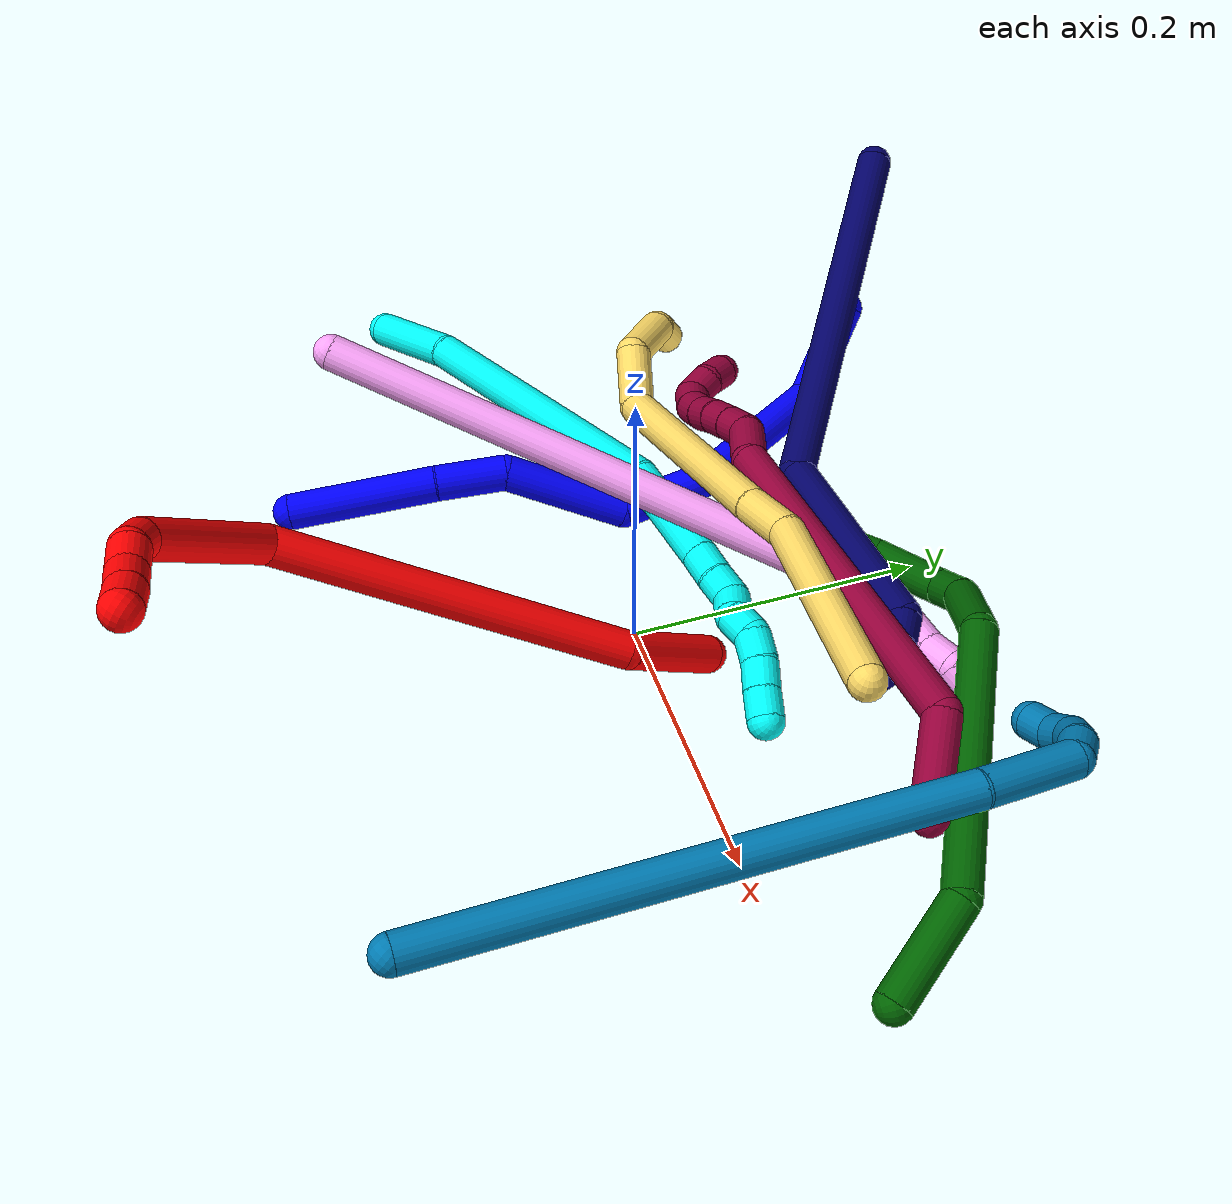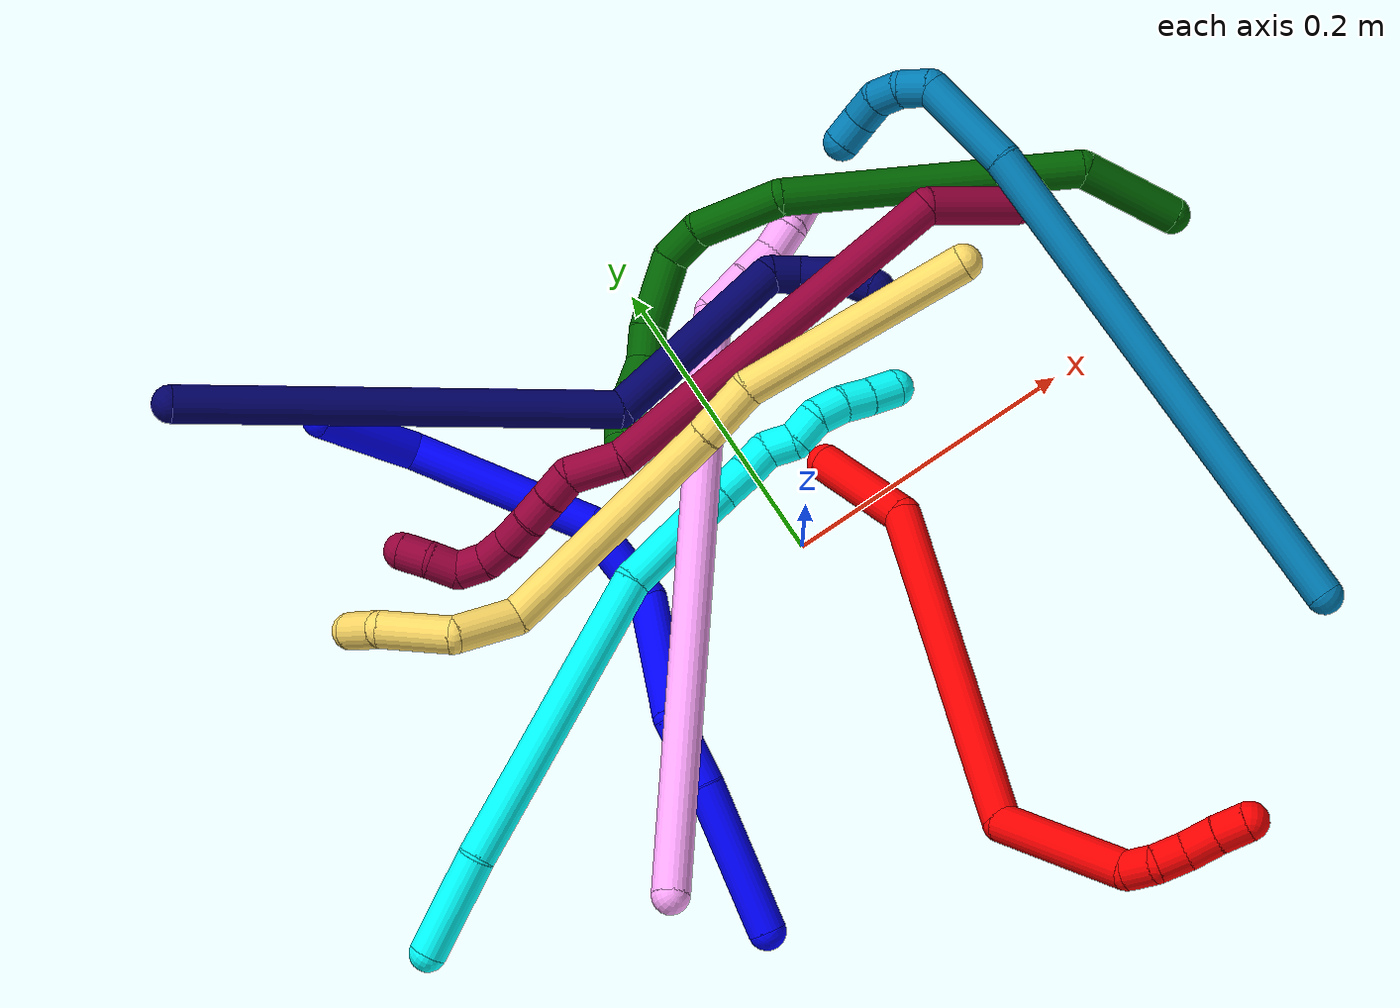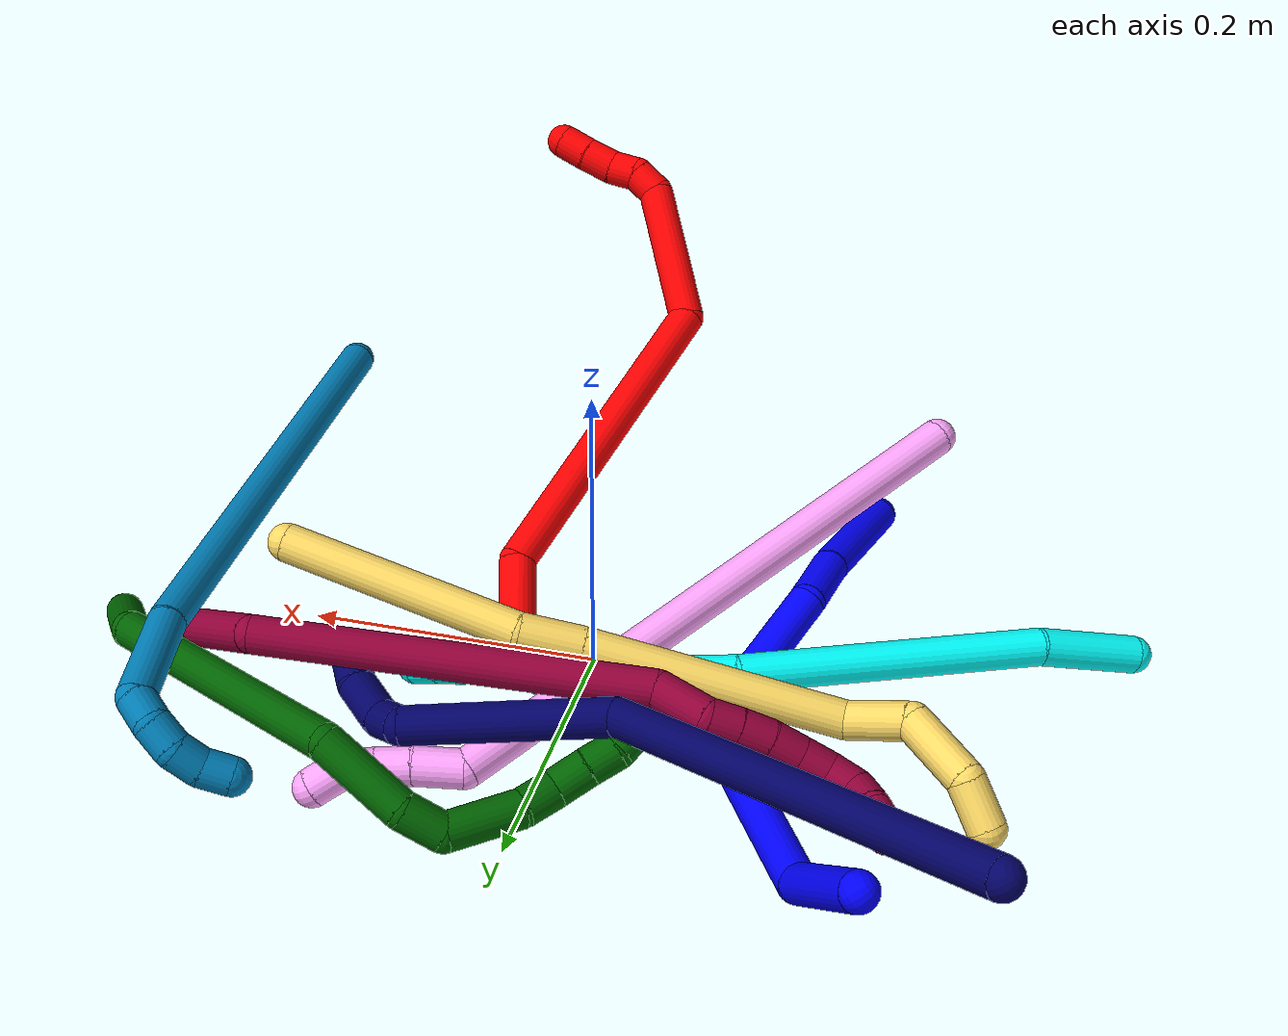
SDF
<sdf version="1.7">
 <world name="default">
  <plugin name="TubeGeneratorPlugin" filename="libtube_generator_plugin.so"/>
  <model name="photoneo_s_sensor">
   <static>1</static>
   <pose>0 0 2 1.57079 1.57079 3.14159</pose>
   <link name="link">
    <inertial><mass>0.1</mass></inertial>
    <sensor name="sensor" type="depth">
     <update_rate>30</update_rate>
     <camera>
      <horizontal_fov>1.22</horizontal_fov>
      <image><width>1920</width><height>1200</height><format>B8G8R8</format></image>
      <clip><near>0.1</near><far>4</far></clip>
      <depth_camera><output>points</output></depth_camera>
     </camera>
     <plugin name="camera_plugin" filename="libgazebo_ros_depth_camera.so">
      <baseline>0.2</baseline>
      <alwaysOn>1</alwaysOn>
      <updateRate>0.0</updateRate>
      <cameraName>camera_ir</cameraName>
      <imageTopicName>/camera/color/image_raw</imageTopicName>
      <cameraInfoTopicName>/camera/color/camera_info</cameraInfoTopicName>
      <depthImageTopicName>/camera/depth/image_raw</depthImageTopicName>
      <depthImageCameraInfoTopicName>/camera/depth/camera_info</depthImageCameraInfoTopicName>
      <pointCloudTopicName>/camera/depth/points</pointCloudTopicName>
      <frameName>fr_optical</frameName>
      <pointCloudCutoff>0.1</pointCloudCutoff>
      <pointCloudCutoffMax>2.0</pointCloudCutoffMax>
      <distortionK1>0</distortionK1>
      <distortionK2>0</distortionK2>
      <distortionK3>0</distortionK3>
      <distortionT1>0</distortionT1>
      <distortionT2>0</distortionT2>
      <CxPrime>0</CxPrime>
      <Cx>0</Cx>
      <Cy>0</Cy>
      <focalLength>0</focalLength>
      <hackBaseline>0</hackBaseline>
     </plugin>
    </sensor>
   </link>
  </model>
  <gravity>0 0 -9.8</gravity>
  <magnetic_field>6e-06 2.3e-05 -4.2e-05</magnetic_field>
  <atmosphere type="adiabatic"/>
  <physics name="default_physics" default="0" type="ode">
   <max_step_size>0.003</max_step_size>
   <real_time_factor>1</real_time_factor>
   <real_time_update_rate>1000</real_time_update_rate>
   <max_contacts>10000</max_contacts>
   <ode>
    <solver>
     <type>quick</type>
     <iters>100</iters>
     <sor>1.3</sor>
     <use_dynamic_moi_rescaling>0</use_dynamic_moi_rescaling>
    </solver>
    <constraints>
     <contact_max_correcting_vel>0</contact_max_correcting_vel>
     <contact_surface_layer>0.001</contact_surface_layer>
     <cfm>0</cfm>
     <erp>0.2</erp>
    </constraints>
   </ode>
  </physics>
  <scene><ambient>0.4 0.4 0.4 1</ambient><background>0.7 0.7 0.7 1</background><shadows>0</shadows></scene>
  <audio><device>default</device></audio>
  <spherical_coordinates>
   <surface_model>EARTH_WGS84</surface_model>
   <latitude_deg>0</latitude_deg>
   <longitude_deg>0</longitude_deg>
   <elevation>0</elevation>
   <heading_deg>0</heading_deg>
  </spherical_coordinates>
  <model name="bin">
   <static>1</static>
   <link name="bottom">
    <collision name="collision-bottom">
     <pose>0 0 -0.01 0 -0 0</pose>
     <geometry><box><size>0.8 0.6 0.02</size></box></geometry>
     <surface>
      <friction><ode><mu>100</mu><mu2>100</mu2></ode></friction>
      <contact><collide_bitmask>65535</collide_bitmask></contact>
     </surface>
    </collision>
   </link>
   <link name="west_wall">
    <collision name="collision-west_wall">
     <pose>-0.41 0 0.1 0 -0 0</pose>
     <geometry><box><size>0.02 0.6 0.2</size></box></geometry>
     <surface>
      <friction><ode><mu>100</mu><mu2>100</mu2></ode></friction>
      <contact><collide_bitmask>65535</collide_bitmask></contact>
     </surface>
    </collision>
   </link>
   <link name="east_wall">
    <collision name="collision-east_wall">
     <pose>0.41 0 0.1 0 -0 0</pose>
     <geometry><box><size>0.02 0.6 0.2</size></box></geometry>
     <surface>
      <friction><ode><mu>100</mu><mu2>100</mu2></ode></friction>
      <contact><collide_bitmask>65535</collide_bitmask></contact>
     </surface>
    </collision>
   </link>
   <link name="south_wall">
    <collision name="collision-south_wall">
     <pose>0 -0.31 0.1 0 -0 0</pose>
     <geometry><box><size>0.8 0.02 0.2</size></box></geometry>
     <surface>
      <friction><ode><mu>100</mu><mu2>100</mu2></ode></friction>
      <contact><collide_bitmask>65535</collide_bitmask></contact>
     </surface>
    </collision>
   </link>
   <link name="north_wall">
    <collision name="collision-north_wall">
     <pose>0 0.31 0.1 0 -0 0</pose>
     <geometry><box><size>0.8 0.02 0.2</size></box></geometry>
     <surface>
      <friction><ode><mu>100</mu><mu2>100</mu2></ode></friction>
      <contact><collide_bitmask>65535</collide_bitmask></contact>
     </surface>
    </collision>
   </link>
  </model>
  <model name="1">
   <static>0</static>
   <link name="1">
    <collision name="collision-cylinder-e_1_1_4">
     <pose>0.014513 0.045211 -0.019515 -1.97827 0.286604 -0.432032</pose>
     <geometry><cylinder><radius>0.0125</radius><length>0.102674</length></cylinder></geometry>
     <surface>
      <friction><ode><mu>1.16</mu><mu2>1.16</mu2><slip1>0</slip1><slip2>0</slip2></ode></friction>
      <contact><ode><kp>1e+06</kp><kd>1</kd><max_vel>0</max_vel><min_depth>0.001</min_depth></ode></contact>
     </surface>
    </collision>
    <visual name="visual-cylinder-e_1_1_4">
     <pose>0.014513 0.045211 -0.019515 -1.97827 0.286604 -0.432032</pose>
     <geometry><cylinder><radius>0.0125</radius><length>0.102674</length></cylinder></geometry>
     <material><ambient>0 0 1 1</ambient></material>
    </visual>
    <collision name="collision-cylinder-e_2_4_5">
     <pose>0.033302 0.112284 -0.048863 -1.9935 0.176544 -0.272015</pose>
     <geometry><cylinder><radius>0.0125</radius><length>0.048701</length></cylinder></geometry>
     <surface>
      <friction><ode><mu>1.16</mu><mu2>1.16</mu2><slip1>0</slip1><slip2>0</slip2></ode></friction>
      <contact><ode><kp>1e+06</kp><kd>1</kd><max_vel>0</max_vel><min_depth>0.001</min_depth></ode></contact>
     </surface>
    </collision>
    <visual name="visual-cylinder-e_2_4_5">
     <pose>0.033302 0.112284 -0.048863 -1.9935 0.176544 -0.272015</pose>
     <geometry><cylinder><radius>0.0125</radius><length>0.048701</length></cylinder></geometry>
     <material><ambient>0 0 1 1</ambient></material>
    </visual>
    <collision name="collision-cylinder-e_3_5_6">
     <pose>0.036875 0.162937 -0.091548 -2.42198 -0.01612 0.042845</pose>
     <geometry><cylinder><radius>0.0125</radius><length>0.087375</length></cylinder></geometry>
     <surface>
      <friction><ode><mu>1.16</mu><mu2>1.16</mu2><slip1>0</slip1><slip2>0</slip2></ode></friction>
      <contact><ode><kp>1e+06</kp><kd>1</kd><max_vel>0</max_vel><min_depth>0.001</min_depth></ode></contact>
     </surface>
    </collision>
    <visual name="visual-cylinder-e_3_5_6">
     <pose>0.036875 0.162937 -0.091548 -2.42198 -0.01612 0.042845</pose>
     <geometry><cylinder><radius>0.0125</radius><length>0.087375</length></cylinder></geometry>
     <material><ambient>0 0 1 1</ambient></material>
    </visual>
    <collision name="collision-cylinder-e_4_6_7">
     <pose>0.039993 0.221229 -0.130757 -1.78306 0.125998 -0.155935</pose>
     <geometry><cylinder><radius>0.0125</radius><length>0.060839</length></cylinder></geometry>
     <surface>
      <friction><ode><mu>1.16</mu><mu2>1.16</mu2><slip1>0</slip1><slip2>0</slip2></ode></friction>
      <contact><ode><kp>1e+06</kp><kd>1</kd><max_vel>0</max_vel><min_depth>0.001</min_depth></ode></contact>
     </surface>
    </collision>
    <visual name="visual-cylinder-e_4_6_7">
     <pose>0.039993 0.221229 -0.130757 -1.78306 0.125998 -0.155935</pose>
     <geometry><cylinder><radius>0.0125</radius><length>0.060839</length></cylinder></geometry>
     <material><ambient>0 0 1 1</ambient></material>
    </visual>
    <collision name="collision-cylinder-e_5_7_8">
     <pose>0.024171 0.310887 -0.130435 -1.4602 -0.31383 0.281366</pose>
     <geometry><cylinder><radius>0.0125</radius><length>0.127271</length></cylinder></geometry>
     <surface>
      <friction><ode><mu>1.16</mu><mu2>1.16</mu2><slip1>0</slip1><slip2>0</slip2></ode></friction>
      <contact><ode><kp>1e+06</kp><kd>1</kd><max_vel>0</max_vel><min_depth>0.001</min_depth></ode></contact>
     </surface>
    </collision>
    <visual name="visual-cylinder-e_5_7_8">
     <pose>0.024171 0.310887 -0.130435 -1.4602 -0.31383 0.281366</pose>
     <geometry><cylinder><radius>0.0125</radius><length>0.127271</length></cylinder></geometry>
     <material><ambient>0 0 1 1</ambient></material>
    </visual>
    <collision name="collision-cylinder-e_6_8_2">
     <pose>0.011749 0.401009 -0.104073 -0.989643 0.198796 -0.107521</pose>
     <geometry><cylinder><radius>0.0125</radius><length>0.07314</length></cylinder></geometry>
     <surface>
      <friction><ode><mu>1.16</mu><mu2>1.16</mu2><slip1>0</slip1><slip2>0</slip2></ode></friction>
      <contact><ode><kp>1e+06</kp><kd>1</kd><max_vel>0</max_vel><min_depth>0.001</min_depth></ode></contact>
     </surface>
    </collision>
    <visual name="visual-cylinder-e_6_8_2">
     <pose>0.011749 0.401009 -0.104073 -0.989643 0.198796 -0.107521</pose>
     <geometry><cylinder><radius>0.0125</radius><length>0.07314</length></cylinder></geometry>
     <material><ambient>0 0 1 1</ambient></material>
    </visual>
    <collision name="collision-sphere-2">
     <pose>0.018971 0.430973 -0.084392 0 -0 0</pose>
     <geometry><sphere><radius>0.0125</radius></sphere></geometry>
     <surface>
      <friction><ode><mu>1.16</mu><mu2>1.16</mu2><slip1>0</slip1><slip2>0</slip2></ode></friction>
      <contact><ode><kp>1e+06</kp><kd>1</kd><max_vel>0</max_vel><min_depth>0.001</min_depth></ode></contact>
     </surface>
    </collision>
    <visual name="visual-sphere-2">
     <pose>0.018971 0.430973 -0.084392 0 -0 0</pose>
     <geometry><sphere><radius>0.0125</radius></sphere></geometry>
     <material><ambient>0 0 1 1</ambient></material>
    </visual>
    <collision name="collision-sphere-4">
     <pose>0.029026 0.090422 -0.039029 0 -0 0</pose>
     <geometry><sphere><radius>0.0125</radius></sphere></geometry>
     <surface>
      <friction><ode><mu>1.16</mu><mu2>1.16</mu2><slip1>0</slip1><slip2>0</slip2></ode></friction>
      <contact><ode><kp>1e+06</kp><kd>1</kd><max_vel>0</max_vel><min_depth>0.001</min_depth></ode></contact>
     </surface>
    </collision>
    <visual name="visual-sphere-4">
     <pose>0.029026 0.090422 -0.039029 0 -0 0</pose>
     <geometry><sphere><radius>0.0125</radius></sphere></geometry>
     <material><ambient>0 0 1 1</ambient></material>
    </visual>
    <collision name="collision-sphere-1">
     <geometry><sphere><radius>0.0125</radius></sphere></geometry>
     <surface>
      <friction><ode><mu>1.16</mu><mu2>1.16</mu2><slip1>0</slip1><slip2>0</slip2></ode></friction>
      <contact><ode><kp>1e+06</kp><kd>1</kd><max_vel>0</max_vel><min_depth>0.001</min_depth></ode></contact>
     </surface>
    </collision>
    <visual name="visual-sphere-1">
     <geometry><sphere><radius>0.0125</radius></sphere></geometry>
     <material><ambient>0 0 1 1</ambient></material>
    </visual>
    <collision name="collision-sphere-8">
     <pose>0.004527 0.371045 -0.123755 0 -0 0</pose>
     <geometry><sphere><radius>0.0125</radius></sphere></geometry>
     <surface>
      <friction><ode><mu>1.16</mu><mu2>1.16</mu2><slip1>0</slip1><slip2>0</slip2></ode></friction>
      <contact><ode><kp>1e+06</kp><kd>1</kd><max_vel>0</max_vel><min_depth>0.001</min_depth></ode></contact>
     </surface>
    </collision>
    <visual name="visual-sphere-8">
     <pose>0.004527 0.371045 -0.123755 0 -0 0</pose>
     <geometry><sphere><radius>0.0125</radius></sphere></geometry>
     <material><ambient>0 0 1 1</ambient></material>
    </visual>
    <collision name="collision-sphere-5">
     <pose>0.037579 0.134146 -0.058697 0 -0 0</pose>
     <geometry><sphere><radius>0.0125</radius></sphere></geometry>
     <surface>
      <friction><ode><mu>1.16</mu><mu2>1.16</mu2><slip1>0</slip1><slip2>0</slip2></ode></friction>
      <contact><ode><kp>1e+06</kp><kd>1</kd><max_vel>0</max_vel><min_depth>0.001</min_depth></ode></contact>
     </surface>
    </collision>
    <visual name="visual-sphere-5">
     <pose>0.037579 0.134146 -0.058697 0 -0 0</pose>
     <geometry><sphere><radius>0.0125</radius></sphere></geometry>
     <material><ambient>0 0 1 1</ambient></material>
    </visual>
    <collision name="collision-sphere-6">
     <pose>0.03617 0.191728 -0.1244 0 -0 0</pose>
     <geometry><sphere><radius>0.0125</radius></sphere></geometry>
     <surface>
      <friction><ode><mu>1.16</mu><mu2>1.16</mu2><slip1>0</slip1><slip2>0</slip2></ode></friction>
      <contact><ode><kp>1e+06</kp><kd>1</kd><max_vel>0</max_vel><min_depth>0.001</min_depth></ode></contact>
     </surface>
    </collision>
    <visual name="visual-sphere-6">
     <pose>0.03617 0.191728 -0.1244 0 -0 0</pose>
     <geometry><sphere><radius>0.0125</radius></sphere></geometry>
     <material><ambient>0 0 1 1</ambient></material>
    </visual>
    <collision name="collision-sphere-7">
     <pose>0.043816 0.250729 -0.137115 0 -0 0</pose>
     <geometry><sphere><radius>0.0125</radius></sphere></geometry>
     <surface>
      <friction><ode><mu>1.16</mu><mu2>1.16</mu2><slip1>0</slip1><slip2>0</slip2></ode></friction>
      <contact><ode><kp>1e+06</kp><kd>1</kd><max_vel>0</max_vel><min_depth>0.001</min_depth></ode></contact>
     </surface>
    </collision>
    <visual name="visual-sphere-7">
     <pose>0.043816 0.250729 -0.137115 0 -0 0</pose>
     <geometry><sphere><radius>0.0125</radius></sphere></geometry>
     <material><ambient>0 0 1 1</ambient></material>
    </visual>
    <inertial>
     <pose>0.025405 0.213406 -0.0891 0 -0 0</pose>
     <mass>0.5</mass>
     <inertia>
      <ixx>0.000372</ixx>
      <ixy>0</ixy>
      <ixz>0</ixz>
      <iyy>1.3e-05</iyy>
      <iyz>0</iyz>
      <izz>-0.000338</izz>
     </inertia>
    </inertial>
   </link>
   <pose>-0.16166 -0.196694 0.024489 0.248114 -0.954057 0.105483</pose>
  </model>
  <model name="2">
   <static>0</static>
   <link name="2">
    <collision name="collision-cylinder-e_1_1_4">
     <pose>0.004676 -0.029436 0.024141 0.883897 0.122222 0.057887</pose>
     <geometry><cylinder><radius>0.0125</radius><length>0.07671</length></cylinder></geometry>
     <surface>
      <friction><ode><mu>1.16</mu><mu2>1.16</mu2><slip1>0</slip1><slip2>0</slip2></ode></friction>
      <contact><ode><kp>1e+06</kp><kd>1</kd><max_vel>0</max_vel><min_depth>0.001</min_depth></ode></contact>
     </surface>
    </collision>
    <visual name="visual-cylinder-e_1_1_4">
     <pose>0.004676 -0.029436 0.024141 0.883897 0.122222 0.057887</pose>
     <geometry><cylinder><radius>0.0125</radius><length>0.07671</length></cylinder></geometry>
     <material><ambient>1 0 0 1</ambient></material>
    </visual>
    <collision name="collision-cylinder-e_2_4_5">
     <pose>0.003218 -0.099518 0.158414 0.353568 -0.052208 -0.009329</pose>
     <geometry><cylinder><radius>0.0125</radius><length>0.235107</length></cylinder></geometry>
     <surface>
      <friction><ode><mu>1.16</mu><mu2>1.16</mu2><slip1>0</slip1><slip2>0</slip2></ode></friction>
      <contact><ode><kp>1e+06</kp><kd>1</kd><max_vel>0</max_vel><min_depth>0.001</min_depth></ode></contact>
     </surface>
    </collision>
    <visual name="visual-cylinder-e_2_4_5">
     <pose>0.003218 -0.099518 0.158414 0.353568 -0.052208 -0.009329</pose>
     <geometry><cylinder><radius>0.0125</radius><length>0.235107</length></cylinder></geometry>
     <material><ambient>1 0 0 1</ambient></material>
    </visual>
    <collision name="collision-cylinder-e_3_5_6">
     <pose>0.008813 -0.184766 0.292926 1.07055 0.226798 0.134871</pose>
     <geometry><cylinder><radius>0.0125</radius><length>0.10433</length></cylinder></geometry>
     <surface>
      <friction><ode><mu>1.16</mu><mu2>1.16</mu2><slip1>0</slip1><slip2>0</slip2></ode></friction>
      <contact><ode><kp>1e+06</kp><kd>1</kd><max_vel>0</max_vel><min_depth>0.001</min_depth></ode></contact>
     </surface>
    </collision>
    <visual name="visual-cylinder-e_3_5_6">
     <pose>0.008813 -0.184766 0.292926 1.07055 0.226798 0.134871</pose>
     <geometry><cylinder><radius>0.0125</radius><length>0.10433</length></cylinder></geometry>
     <material><ambient>1 0 0 1</ambient></material>
    </visual>
    <collision name="collision-cylinder-e_4_6_7">
     <pose>0.023185 -0.23901 0.316759 1.62744 0.26705 0.282421</pose>
     <geometry><cylinder><radius>0.0125</radius><length>0.020027</length></cylinder></geometry>
     <surface>
      <friction><ode><mu>1.16</mu><mu2>1.16</mu2><slip1>0</slip1><slip2>0</slip2></ode></friction>
      <contact><ode><kp>1e+06</kp><kd>1</kd><max_vel>0</max_vel><min_depth>0.001</min_depth></ode></contact>
     </surface>
    </collision>
    <visual name="visual-cylinder-e_4_6_7">
     <pose>0.023185 -0.23901 0.316759 1.62744 0.26705 0.282421</pose>
     <geometry><cylinder><radius>0.0125</radius><length>0.020027</length></cylinder></geometry>
     <material><ambient>1 0 0 1</ambient></material>
    </visual>
    <collision name="collision-cylinder-e_5_7_8">
     <pose>0.025333 -0.257848 0.311982 2.00203 -0.04885 -0.076227</pose>
     <geometry><cylinder><radius>0.0125</radius><length>0.020268</length></cylinder></geometry>
     <surface>
      <friction><ode><mu>1.16</mu><mu2>1.16</mu2><slip1>0</slip1><slip2>0</slip2></ode></friction>
      <contact><ode><kp>1e+06</kp><kd>1</kd><max_vel>0</max_vel><min_depth>0.001</min_depth></ode></contact>
     </surface>
    </collision>
    <visual name="visual-cylinder-e_5_7_8">
     <pose>0.025333 -0.257848 0.311982 2.00203 -0.04885 -0.076227</pose>
     <geometry><cylinder><radius>0.0125</radius><length>0.020268</length></cylinder></geometry>
     <material><ambient>1 0 0 1</ambient></material>
    </visual>
    <collision name="collision-cylinder-e_6_8_9">
     <pose>0.027269 -0.277249 0.303689 1.94955 0.217781 0.319589</pose>
     <geometry><cylinder><radius>0.0125</radius><length>0.022498</length></cylinder></geometry>
     <surface>
      <friction><ode><mu>1.16</mu><mu2>1.16</mu2><slip1>0</slip1><slip2>0</slip2></ode></friction>
      <contact><ode><kp>1e+06</kp><kd>1</kd><max_vel>0</max_vel><min_depth>0.001</min_depth></ode></contact>
     </surface>
    </collision>
    <visual name="visual-cylinder-e_6_8_9">
     <pose>0.027269 -0.277249 0.303689 1.94955 0.217781 0.319589</pose>
     <geometry><cylinder><radius>0.0125</radius><length>0.022498</length></cylinder></geometry>
     <material><ambient>1 0 0 1</ambient></material>
    </visual>
    <collision name="collision-cylinder-e_7_9_2">
     <pose>0.031619 -0.297332 0.29653 1.8747 0.183357 0.249072</pose>
     <geometry><cylinder><radius>0.0125</radius><length>0.021059</length></cylinder></geometry>
     <surface>
      <friction><ode><mu>1.16</mu><mu2>1.16</mu2><slip1>0</slip1><slip2>0</slip2></ode></friction>
      <contact><ode><kp>1e+06</kp><kd>1</kd><max_vel>0</max_vel><min_depth>0.001</min_depth></ode></contact>
     </surface>
    </collision>
    <visual name="visual-cylinder-e_7_9_2">
     <pose>0.031619 -0.297332 0.29653 1.8747 0.183357 0.249072</pose>
     <geometry><cylinder><radius>0.0125</radius><length>0.021059</length></cylinder></geometry>
     <material><ambient>1 0 0 1</ambient></material>
    </visual>
    <collision name="collision-sphere-2">
     <pose>0.033539 -0.307211 0.293432 0 -0 0</pose>
     <geometry><sphere><radius>0.0125</radius></sphere></geometry>
     <surface>
      <friction><ode><mu>1.16</mu><mu2>1.16</mu2><slip1>0</slip1><slip2>0</slip2></ode></friction>
      <contact><ode><kp>1e+06</kp><kd>1</kd><max_vel>0</max_vel><min_depth>0.001</min_depth></ode></contact>
     </surface>
    </collision>
    <visual name="visual-sphere-2">
     <pose>0.033539 -0.307211 0.293432 0 -0 0</pose>
     <geometry><sphere><radius>0.0125</radius></sphere></geometry>
     <material><ambient>1 0 0 1</ambient></material>
    </visual>
    <collision name="collision-sphere-9">
     <pose>0.029699 -0.287454 0.299628 0 -0 0</pose>
     <geometry><sphere><radius>0.0125</radius></sphere></geometry>
     <surface>
      <friction><ode><mu>1.16</mu><mu2>1.16</mu2><slip1>0</slip1><slip2>0</slip2></ode></friction>
      <contact><ode><kp>1e+06</kp><kd>1</kd><max_vel>0</max_vel><min_depth>0.001</min_depth></ode></contact>
     </surface>
    </collision>
    <visual name="visual-sphere-9">
     <pose>0.029699 -0.287454 0.299628 0 -0 0</pose>
     <geometry><sphere><radius>0.0125</radius></sphere></geometry>
     <material><ambient>1 0 0 1</ambient></material>
    </visual>
    <collision name="collision-sphere-4">
     <pose>0.009352 -0.058871 0.048282 0 -0 0</pose>
     <geometry><sphere><radius>0.0125</radius></sphere></geometry>
     <surface>
      <friction><ode><mu>1.16</mu><mu2>1.16</mu2><slip1>0</slip1><slip2>0</slip2></ode></friction>
      <contact><ode><kp>1e+06</kp><kd>1</kd><max_vel>0</max_vel><min_depth>0.001</min_depth></ode></contact>
     </surface>
    </collision>
    <visual name="visual-sphere-4">
     <pose>0.009352 -0.058871 0.048282 0 -0 0</pose>
     <geometry><sphere><radius>0.0125</radius></sphere></geometry>
     <material><ambient>1 0 0 1</ambient></material>
    </visual>
    <collision name="collision-sphere-1">
     <geometry><sphere><radius>0.0125</radius></sphere></geometry>
     <surface>
      <friction><ode><mu>1.16</mu><mu2>1.16</mu2><slip1>0</slip1><slip2>0</slip2></ode></friction>
      <contact><ode><kp>1e+06</kp><kd>1</kd><max_vel>0</max_vel><min_depth>0.001</min_depth></ode></contact>
     </surface>
    </collision>
    <visual name="visual-sphere-1">
     <geometry><sphere><radius>0.0125</radius></sphere></geometry>
     <material><ambient>1 0 0 1</ambient></material>
    </visual>
    <collision name="collision-sphere-8">
     <pose>0.024838 -0.267044 0.307751 0 -0 0</pose>
     <geometry><sphere><radius>0.0125</radius></sphere></geometry>
     <surface>
      <friction><ode><mu>1.16</mu><mu2>1.16</mu2><slip1>0</slip1><slip2>0</slip2></ode></friction>
      <contact><ode><kp>1e+06</kp><kd>1</kd><max_vel>0</max_vel><min_depth>0.001</min_depth></ode></contact>
     </surface>
    </collision>
    <visual name="visual-sphere-8">
     <pose>0.024838 -0.267044 0.307751 0 -0 0</pose>
     <geometry><sphere><radius>0.0125</radius></sphere></geometry>
     <material><ambient>1 0 0 1</ambient></material>
    </visual>
    <collision name="collision-sphere-5">
     <pose>-0.002916 -0.140166 0.268546 0 -0 0</pose>
     <geometry><sphere><radius>0.0125</radius></sphere></geometry>
     <surface>
      <friction><ode><mu>1.16</mu><mu2>1.16</mu2><slip1>0</slip1><slip2>0</slip2></ode></friction>
      <contact><ode><kp>1e+06</kp><kd>1</kd><max_vel>0</max_vel><min_depth>0.001</min_depth></ode></contact>
     </surface>
    </collision>
    <visual name="visual-sphere-5">
     <pose>-0.002916 -0.140166 0.268546 0 -0 0</pose>
     <geometry><sphere><radius>0.0125</radius></sphere></geometry>
     <material><ambient>1 0 0 1</ambient></material>
    </visual>
    <collision name="collision-sphere-6">
     <pose>0.020543 -0.229367 0.317306 0 -0 0</pose>
     <geometry><sphere><radius>0.0125</radius></sphere></geometry>
     <surface>
      <friction><ode><mu>1.16</mu><mu2>1.16</mu2><slip1>0</slip1><slip2>0</slip2></ode></friction>
      <contact><ode><kp>1e+06</kp><kd>1</kd><max_vel>0</max_vel><min_depth>0.001</min_depth></ode></contact>
     </surface>
    </collision>
    <visual name="visual-sphere-6">
     <pose>0.020543 -0.229367 0.317306 0 -0 0</pose>
     <geometry><sphere><radius>0.0125</radius></sphere></geometry>
     <material><ambient>1 0 0 1</ambient></material>
    </visual>
    <collision name="collision-sphere-7">
     <pose>0.025828 -0.248653 0.316212 0 -0 0</pose>
     <geometry><sphere><radius>0.0125</radius></sphere></geometry>
     <surface>
      <friction><ode><mu>1.16</mu><mu2>1.16</mu2><slip1>0</slip1><slip2>0</slip2></ode></friction>
      <contact><ode><kp>1e+06</kp><kd>1</kd><max_vel>0</max_vel><min_depth>0.001</min_depth></ode></contact>
     </surface>
    </collision>
    <visual name="visual-sphere-7">
     <pose>0.025828 -0.248653 0.316212 0 -0 0</pose>
     <geometry><sphere><radius>0.0125</radius></sphere></geometry>
     <material><ambient>1 0 0 1</ambient></material>
    </visual>
    <inertial>
     <pose>0.008584 -0.134888 0.190803 0 -0 0</pose>
     <mass>0.5</mass>
     <inertia>
      <ixx>0.001241</ixx>
      <ixy>0</ixy>
      <ixz>0</ixz>
      <iyy>0.001081</iyy>
      <iyz>0</iyz>
      <izz>0.000551</izz>
     </inertia>
    </inertial>
   </link>
   <pose>0.042301 0.036052 0.011498 -0.685262 -1.07695 1.61655</pose>
  </model>
  <model name="3">
   <static>0</static>
   <link name="3">
    <collision name="collision-cylinder-e_1_1_4">
     <pose>0.009263 -0.019694 -0.027786 2.525 0.265573 0.794318</pose>
     <geometry><cylinder><radius>0.0125</radius><length>0.070589</length></cylinder></geometry>
     <surface>
      <friction><ode><mu>1.16</mu><mu2>1.16</mu2><slip1>0</slip1><slip2>0</slip2></ode></friction>
      <contact><ode><kp>1e+06</kp><kd>1</kd><max_vel>0</max_vel><min_depth>0.001</min_depth></ode></contact>
     </surface>
    </collision>
    <visual name="visual-cylinder-e_1_1_4">
     <pose>0.009263 -0.019694 -0.027786 2.525 0.265573 0.794318</pose>
     <geometry><cylinder><radius>0.0125</radius><length>0.070589</length></cylinder></geometry>
     <material><ambient>0.003922 1 0.996078 1</ambient></material>
    </visual>
    <collision name="collision-cylinder-e_2_4_5">
     <pose>0.057688 -0.107232 -0.121977 2.34547 0.391239 0.880726</pose>
     <geometry><cylinder><radius>0.0125</radius><length>0.205389</length></cylinder></geometry>
     <surface>
      <friction><ode><mu>1.16</mu><mu2>1.16</mu2><slip1>0</slip1><slip2>0</slip2></ode></friction>
      <contact><ode><kp>1e+06</kp><kd>1</kd><max_vel>0</max_vel><min_depth>0.001</min_depth></ode></contact>
     </surface>
    </collision>
    <visual name="visual-cylinder-e_2_4_5">
     <pose>0.057688 -0.107232 -0.121977 2.34547 0.391239 0.880726</pose>
     <geometry><cylinder><radius>0.0125</radius><length>0.205389</length></cylinder></geometry>
     <material><ambient>0.003922 1 0.996078 1</ambient></material>
    </visual>
    <collision name="collision-cylinder-e_3_5_6">
     <pose>0.122896 -0.197114 -0.210946 2.36801 0.690319 1.4464</pose>
     <geometry><cylinder><radius>0.0125</radius><length>0.08181</length></cylinder></geometry>
     <surface>
      <friction><ode><mu>1.16</mu><mu2>1.16</mu2><slip1>0</slip1><slip2>0</slip2></ode></friction>
      <contact><ode><kp>1e+06</kp><kd>1</kd><max_vel>0</max_vel><min_depth>0.001</min_depth></ode></contact>
     </surface>
    </collision>
    <visual name="visual-cylinder-e_3_5_6">
     <pose>0.122896 -0.197114 -0.210946 2.36801 0.690319 1.4464</pose>
     <geometry><cylinder><radius>0.0125</radius><length>0.08181</length></cylinder></geometry>
     <material><ambient>0.003922 1 0.996078 1</ambient></material>
    </visual>
    <collision name="collision-cylinder-e_4_6_7">
     <pose>0.156018 -0.224492 -0.239559 2.41826 0.719761 1.56539</pose>
     <geometry><cylinder><radius>0.0125</radius><length>0.021464</length></cylinder></geometry>
     <surface>
      <friction><ode><mu>1.16</mu><mu2>1.16</mu2><slip1>0</slip1><slip2>0</slip2></ode></friction>
      <contact><ode><kp>1e+06</kp><kd>1</kd><max_vel>0</max_vel><min_depth>0.001</min_depth></ode></contact>
     </surface>
    </collision>
    <visual name="visual-cylinder-e_4_6_7">
     <pose>0.156018 -0.224492 -0.239559 2.41826 0.719761 1.56539</pose>
     <geometry><cylinder><radius>0.0125</radius><length>0.021464</length></cylinder></geometry>
     <material><ambient>0.003922 1 0.996078 1</ambient></material>
    </visual>
    <collision name="collision-cylinder-e_5_7_8">
     <pose>0.169337 -0.235817 -0.250797 2.28518 0.667662 1.29949</pose>
     <geometry><cylinder><radius>0.0125</radius><length>0.020171</length></cylinder></geometry>
     <surface>
      <friction><ode><mu>1.16</mu><mu2>1.16</mu2><slip1>0</slip1><slip2>0</slip2></ode></friction>
      <contact><ode><kp>1e+06</kp><kd>1</kd><max_vel>0</max_vel><min_depth>0.001</min_depth></ode></contact>
     </surface>
    </collision>
    <visual name="visual-cylinder-e_5_7_8">
     <pose>0.169337 -0.235817 -0.250797 2.28518 0.667662 1.29949</pose>
     <geometry><cylinder><radius>0.0125</radius><length>0.020171</length></cylinder></geometry>
     <material><ambient>0.003922 1 0.996078 1</ambient></material>
    </visual>
    <collision name="collision-cylinder-e_6_8_9">
     <pose>0.183347 -0.241944 -0.262368 3.11902 0.882691 3.09383</pose>
     <geometry><cylinder><radius>0.0125</radius><length>0.020105</length></cylinder></geometry>
     <surface>
      <friction><ode><mu>1.16</mu><mu2>1.16</mu2><slip1>0</slip1><slip2>0</slip2></ode></friction>
      <contact><ode><kp>1e+06</kp><kd>1</kd><max_vel>0</max_vel><min_depth>0.001</min_depth></ode></contact>
     </surface>
    </collision>
    <visual name="visual-cylinder-e_6_8_9">
     <pose>0.183347 -0.241944 -0.262368 3.11902 0.882691 3.09383</pose>
     <geometry><cylinder><radius>0.0125</radius><length>0.020105</length></cylinder></geometry>
     <material><ambient>0.003922 1 0.996078 1</ambient></material>
    </visual>
    <collision name="collision-cylinder-e_7_9_10">
     <pose>0.196513 -0.247584 -0.275261 2.44045 0.565025 1.34191</pose>
     <geometry><cylinder><radius>0.0125</radius><length>0.020175</length></cylinder></geometry>
     <surface>
      <friction><ode><mu>1.16</mu><mu2>1.16</mu2><slip1>0</slip1><slip2>0</slip2></ode></friction>
      <contact><ode><kp>1e+06</kp><kd>1</kd><max_vel>0</max_vel><min_depth>0.001</min_depth></ode></contact>
     </surface>
    </collision>
    <visual name="visual-cylinder-e_7_9_10">
     <pose>0.196513 -0.247584 -0.275261 2.44045 0.565025 1.34191</pose>
     <geometry><cylinder><radius>0.0125</radius><length>0.020175</length></cylinder></geometry>
     <material><ambient>0.003922 1 0.996078 1</ambient></material>
    </visual>
    <collision name="collision-cylinder-e_8_10_11">
     <pose>0.210479 -0.257124 -0.285049 2.25198 1.0246 1.73541</pose>
     <geometry><cylinder><radius>0.0125</radius><length>0.020045</length></cylinder></geometry>
     <surface>
      <friction><ode><mu>1.16</mu><mu2>1.16</mu2><slip1>0</slip1><slip2>0</slip2></ode></friction>
      <contact><ode><kp>1e+06</kp><kd>1</kd><max_vel>0</max_vel><min_depth>0.001</min_depth></ode></contact>
     </surface>
    </collision>
    <visual name="visual-cylinder-e_8_10_11">
     <pose>0.210479 -0.257124 -0.285049 2.25198 1.0246 1.73541</pose>
     <geometry><cylinder><radius>0.0125</radius><length>0.020045</length></cylinder></geometry>
     <material><ambient>0.003922 1 0.996078 1</ambient></material>
    </visual>
    <collision name="collision-cylinder-e_9_11_12">
     <pose>0.228459 -0.263921 -0.290504 2.24016 1.21408 1.92445</pose>
     <geometry><cylinder><radius>0.0125</radius><length>0.020098</length></cylinder></geometry>
     <surface>
      <friction><ode><mu>1.16</mu><mu2>1.16</mu2><slip1>0</slip1><slip2>0</slip2></ode></friction>
      <contact><ode><kp>1e+06</kp><kd>1</kd><max_vel>0</max_vel><min_depth>0.001</min_depth></ode></contact>
     </surface>
    </collision>
    <visual name="visual-cylinder-e_9_11_12">
     <pose>0.228459 -0.263921 -0.290504 2.24016 1.21408 1.92445</pose>
     <geometry><cylinder><radius>0.0125</radius><length>0.020098</length></cylinder></geometry>
     <material><ambient>0.003922 1 0.996078 1</ambient></material>
    </visual>
    <collision name="collision-cylinder-e_10_12_2">
     <pose>0.247106 -0.269842 -0.295193 2.24082 1.15783 1.86774</pose>
     <geometry><cylinder><radius>0.0125</radius><length>0.020154</length></cylinder></geometry>
     <surface>
      <friction><ode><mu>1.16</mu><mu2>1.16</mu2><slip1>0</slip1><slip2>0</slip2></ode></friction>
      <contact><ode><kp>1e+06</kp><kd>1</kd><max_vel>0</max_vel><min_depth>0.001</min_depth></ode></contact>
     </surface>
    </collision>
    <visual name="visual-cylinder-e_10_12_2">
     <pose>0.247106 -0.269842 -0.295193 2.24082 1.15783 1.86774</pose>
     <geometry><cylinder><radius>0.0125</radius><length>0.020154</length></cylinder></geometry>
     <material><ambient>0.003922 1 0.996078 1</ambient></material>
    </visual>
    <collision name="collision-sphere-2">
     <pose>0.256336 -0.273012 -0.297705 0 -0 0</pose>
     <geometry><sphere><radius>0.0125</radius></sphere></geometry>
     <surface>
      <friction><ode><mu>1.16</mu><mu2>1.16</mu2><slip1>0</slip1><slip2>0</slip2></ode></friction>
      <contact><ode><kp>1e+06</kp><kd>1</kd><max_vel>0</max_vel><min_depth>0.001</min_depth></ode></contact>
     </surface>
    </collision>
    <visual name="visual-sphere-2">
     <pose>0.256336 -0.273012 -0.297705 0 -0 0</pose>
     <geometry><sphere><radius>0.0125</radius></sphere></geometry>
     <material><ambient>0.003922 1 0.996078 1</ambient></material>
    </visual>
    <collision name="collision-sphere-12">
     <pose>0.237876 -0.266672 -0.292682 0 -0 0</pose>
     <geometry><sphere><radius>0.0125</radius></sphere></geometry>
     <surface>
      <friction><ode><mu>1.16</mu><mu2>1.16</mu2><slip1>0</slip1><slip2>0</slip2></ode></friction>
      <contact><ode><kp>1e+06</kp><kd>1</kd><max_vel>0</max_vel><min_depth>0.001</min_depth></ode></contact>
     </surface>
    </collision>
    <visual name="visual-sphere-12">
     <pose>0.237876 -0.266672 -0.292682 0 -0 0</pose>
     <geometry><sphere><radius>0.0125</radius></sphere></geometry>
     <material><ambient>0.003922 1 0.996078 1</ambient></material>
    </visual>
    <collision name="collision-sphere-11">
     <pose>0.219043 -0.261169 -0.288327 0 -0 0</pose>
     <geometry><sphere><radius>0.0125</radius></sphere></geometry>
     <surface>
      <friction><ode><mu>1.16</mu><mu2>1.16</mu2><slip1>0</slip1><slip2>0</slip2></ode></friction>
      <contact><ode><kp>1e+06</kp><kd>1</kd><max_vel>0</max_vel><min_depth>0.001</min_depth></ode></contact>
     </surface>
    </collision>
    <visual name="visual-sphere-11">
     <pose>0.219043 -0.261169 -0.288327 0 -0 0</pose>
     <geometry><sphere><radius>0.0125</radius></sphere></geometry>
     <material><ambient>0.003922 1 0.996078 1</ambient></material>
    </visual>
    <collision name="collision-sphere-10">
     <pose>0.201915 -0.25308 -0.28177 0 -0 0</pose>
     <geometry><sphere><radius>0.0125</radius></sphere></geometry>
     <surface>
      <friction><ode><mu>1.16</mu><mu2>1.16</mu2><slip1>0</slip1><slip2>0</slip2></ode></friction>
      <contact><ode><kp>1e+06</kp><kd>1</kd><max_vel>0</max_vel><min_depth>0.001</min_depth></ode></contact>
     </surface>
    </collision>
    <visual name="visual-sphere-10">
     <pose>0.201915 -0.25308 -0.28177 0 -0 0</pose>
     <geometry><sphere><radius>0.0125</radius></sphere></geometry>
     <material><ambient>0.003922 1 0.996078 1</ambient></material>
    </visual>
    <collision name="collision-sphere-9">
     <pose>0.191112 -0.242088 -0.268751 0 -0 0</pose>
     <geometry><sphere><radius>0.0125</radius></sphere></geometry>
     <surface>
      <friction><ode><mu>1.16</mu><mu2>1.16</mu2><slip1>0</slip1><slip2>0</slip2></ode></friction>
      <contact><ode><kp>1e+06</kp><kd>1</kd><max_vel>0</max_vel><min_depth>0.001</min_depth></ode></contact>
     </surface>
    </collision>
    <visual name="visual-sphere-9">
     <pose>0.191112 -0.242088 -0.268751 0 -0 0</pose>
     <geometry><sphere><radius>0.0125</radius></sphere></geometry>
     <material><ambient>0.003922 1 0.996078 1</ambient></material>
    </visual>
    <collision name="collision-sphere-4">
     <pose>0.018527 -0.039387 -0.055571 0 -0 0</pose>
     <geometry><sphere><radius>0.0125</radius></sphere></geometry>
     <surface>
      <friction><ode><mu>1.16</mu><mu2>1.16</mu2><slip1>0</slip1><slip2>0</slip2></ode></friction>
      <contact><ode><kp>1e+06</kp><kd>1</kd><max_vel>0</max_vel><min_depth>0.001</min_depth></ode></contact>
     </surface>
    </collision>
    <visual name="visual-sphere-4">
     <pose>0.018527 -0.039387 -0.055571 0 -0 0</pose>
     <geometry><sphere><radius>0.0125</radius></sphere></geometry>
     <material><ambient>0.003922 1 0.996078 1</ambient></material>
    </visual>
    <collision name="collision-sphere-1">
     <geometry><sphere><radius>0.0125</radius></sphere></geometry>
     <surface>
      <friction><ode><mu>1.16</mu><mu2>1.16</mu2><slip1>0</slip1><slip2>0</slip2></ode></friction>
      <contact><ode><kp>1e+06</kp><kd>1</kd><max_vel>0</max_vel><min_depth>0.001</min_depth></ode></contact>
     </surface>
    </collision>
    <visual name="visual-sphere-1">
     <geometry><sphere><radius>0.0125</radius></sphere></geometry>
     <material><ambient>0.003922 1 0.996078 1</ambient></material>
    </visual>
    <collision name="collision-sphere-8">
     <pose>0.175582 -0.2418 -0.255986 0 -0 0</pose>
     <geometry><sphere><radius>0.0125</radius></sphere></geometry>
     <surface>
      <friction><ode><mu>1.16</mu><mu2>1.16</mu2><slip1>0</slip1><slip2>0</slip2></ode></friction>
      <contact><ode><kp>1e+06</kp><kd>1</kd><max_vel>0</max_vel><min_depth>0.001</min_depth></ode></contact>
     </surface>
    </collision>
    <visual name="visual-sphere-8">
     <pose>0.175582 -0.2418 -0.255986 0 -0 0</pose>
     <geometry><sphere><radius>0.0125</radius></sphere></geometry>
     <material><ambient>0.003922 1 0.996078 1</ambient></material>
    </visual>
    <collision name="collision-sphere-5">
     <pose>0.096849 -0.175077 -0.188382 0 -0 0</pose>
     <geometry><sphere><radius>0.0125</radius></sphere></geometry>
     <surface>
      <friction><ode><mu>1.16</mu><mu2>1.16</mu2><slip1>0</slip1><slip2>0</slip2></ode></friction>
      <contact><ode><kp>1e+06</kp><kd>1</kd><max_vel>0</max_vel><min_depth>0.001</min_depth></ode></contact>
     </surface>
    </collision>
    <visual name="visual-sphere-5">
     <pose>0.096849 -0.175077 -0.188382 0 -0 0</pose>
     <geometry><sphere><radius>0.0125</radius></sphere></geometry>
     <material><ambient>0.003922 1 0.996078 1</ambient></material>
    </visual>
    <collision name="collision-sphere-6">
     <pose>0.148944 -0.219151 -0.23351 0 -0 0</pose>
     <geometry><sphere><radius>0.0125</radius></sphere></geometry>
     <surface>
      <friction><ode><mu>1.16</mu><mu2>1.16</mu2><slip1>0</slip1><slip2>0</slip2></ode></friction>
      <contact><ode><kp>1e+06</kp><kd>1</kd><max_vel>0</max_vel><min_depth>0.001</min_depth></ode></contact>
     </surface>
    </collision>
    <visual name="visual-sphere-6">
     <pose>0.148944 -0.219151 -0.23351 0 -0 0</pose>
     <geometry><sphere><radius>0.0125</radius></sphere></geometry>
     <material><ambient>0.003922 1 0.996078 1</ambient></material>
    </visual>
    <collision name="collision-sphere-7">
     <pose>0.163093 -0.229833 -0.245608 0 -0 0</pose>
     <geometry><sphere><radius>0.0125</radius></sphere></geometry>
     <surface>
      <friction><ode><mu>1.16</mu><mu2>1.16</mu2><slip1>0</slip1><slip2>0</slip2></ode></friction>
      <contact><ode><kp>1e+06</kp><kd>1</kd><max_vel>0</max_vel><min_depth>0.001</min_depth></ode></contact>
     </surface>
    </collision>
    <visual name="visual-sphere-7">
     <pose>0.163093 -0.229833 -0.245608 0 -0 0</pose>
     <geometry><sphere><radius>0.0125</radius></sphere></geometry>
     <material><ambient>0.003922 1 0.996078 1</ambient></material>
    </visual>
    <inertial>
     <pose>0.101525 -0.149743 -0.165605 0 -0 0</pose>
     <mass>0.5</mass>
     <inertia>
      <ixx>0.001061</ixx>
      <ixy>0</ixy>
      <ixz>0</ixz>
      <iyy>0.000401</iyy>
      <iyz>0</iyz>
      <izz>0.000181</izz>
     </inertia>
    </inertial>
   </link>
   <pose>-0.350814 -0.084769 0.012494 2.59962 0.422614 -0.6546</pose>
  </model>
  <model name="4">
   <static>0</static>
   <link name="4">
    <collision name="collision-cylinder-e_1_1_4">
     <pose>0.187856 0.072219 -0.00308 -1.61342 1.20347 -1.24356</pose>
     <geometry><cylinder><radius>0.0125</radius><length>0.402566</length></cylinder></geometry>
     <surface>
      <friction><ode><mu>1.16</mu><mu2>1.16</mu2><slip1>0</slip1><slip2>0</slip2></ode></friction>
      <contact><ode><kp>1e+06</kp><kd>1</kd><max_vel>0</max_vel><min_depth>0.001</min_depth></ode></contact>
     </surface>
    </collision>
    <visual name="visual-cylinder-e_1_1_4">
     <pose>0.187856 0.072219 -0.00308 -1.61342 1.20347 -1.24356</pose>
     <geometry><cylinder><radius>0.0125</radius><length>0.402566</length></cylinder></geometry>
     <material><ambient>1 0.65098 0.996078 1</ambient></material>
    </visual>
    <collision name="collision-cylinder-e_2_4_5">
     <pose>0.389574 0.141318 0.001268 0.397612 1.04433 0.230834</pose>
     <geometry><cylinder><radius>0.0125</radius><length>0.032068</length></cylinder></geometry>
     <surface>
      <friction><ode><mu>1.16</mu><mu2>1.16</mu2><slip1>0</slip1><slip2>0</slip2></ode></friction>
      <contact><ode><kp>1e+06</kp><kd>1</kd><max_vel>0</max_vel><min_depth>0.001</min_depth></ode></contact>
     </surface>
    </collision>
    <visual name="visual-cylinder-e_2_4_5">
     <pose>0.389574 0.141318 0.001268 0.397612 1.04433 0.230834</pose>
     <geometry><cylinder><radius>0.0125</radius><length>0.032068</length></cylinder></geometry>
     <material><ambient>1 0.65098 0.996078 1</ambient></material>
    </visual>
    <collision name="collision-cylinder-e_3_5_6">
     <pose>0.414133 0.135465 0.012771 0.590817 1.14071 0.385565</pose>
     <geometry><cylinder><radius>0.0125</radius><length>0.023537</length></cylinder></geometry>
     <surface>
      <friction><ode><mu>1.16</mu><mu2>1.16</mu2><slip1>0</slip1><slip2>0</slip2></ode></friction>
      <contact><ode><kp>1e+06</kp><kd>1</kd><max_vel>0</max_vel><min_depth>0.001</min_depth></ode></contact>
     </surface>
    </collision>
    <visual name="visual-cylinder-e_3_5_6">
     <pose>0.414133 0.135465 0.012771 0.590817 1.14071 0.385565</pose>
     <geometry><cylinder><radius>0.0125</radius><length>0.023537</length></cylinder></geometry>
     <material><ambient>1 0.65098 0.996078 1</ambient></material>
    </visual>
    <collision name="collision-cylinder-e_4_6_7">
     <pose>0.434206 0.132531 0.021028 0.0478 1.15081 0.031007</pose>
     <geometry><cylinder><radius>0.0125</radius><length>0.020536</length></cylinder></geometry>
     <surface>
      <friction><ode><mu>1.16</mu><mu2>1.16</mu2><slip1>0</slip1><slip2>0</slip2></ode></friction>
      <contact><ode><kp>1e+06</kp><kd>1</kd><max_vel>0</max_vel><min_depth>0.001</min_depth></ode></contact>
     </surface>
    </collision>
    <visual name="visual-cylinder-e_4_6_7">
     <pose>0.434206 0.132531 0.021028 0.0478 1.15081 0.031007</pose>
     <geometry><cylinder><radius>0.0125</radius><length>0.020536</length></cylinder></geometry>
     <material><ambient>1 0.65098 0.996078 1</ambient></material>
    </visual>
    <collision name="collision-cylinder-e_5_7_2">
     <pose>0.454142 0.131636 0.024046 2.60303 1.44303 2.53362</pose>
     <geometry><cylinder><radius>0.0125</radius><length>0.021293</length></cylinder></geometry>
     <surface>
      <friction><ode><mu>1.16</mu><mu2>1.16</mu2><slip1>0</slip1><slip2>0</slip2></ode></friction>
      <contact><ode><kp>1e+06</kp><kd>1</kd><max_vel>0</max_vel><min_depth>0.001</min_depth></ode></contact>
     </surface>
    </collision>
    <visual name="visual-cylinder-e_5_7_2">
     <pose>0.454142 0.131636 0.024046 2.60303 1.44303 2.53362</pose>
     <geometry><cylinder><radius>0.0125</radius><length>0.021293</length></cylinder></geometry>
     <material><ambient>1 0.65098 0.996078 1</ambient></material>
    </visual>
    <collision name="collision-sphere-2">
     <pose>0.464701 0.13094 0.022881 0 -0 0</pose>
     <geometry><sphere><radius>0.0125</radius></sphere></geometry>
     <surface>
      <friction><ode><mu>1.16</mu><mu2>1.16</mu2><slip1>0</slip1><slip2>0</slip2></ode></friction>
      <contact><ode><kp>1e+06</kp><kd>1</kd><max_vel>0</max_vel><min_depth>0.001</min_depth></ode></contact>
     </surface>
    </collision>
    <visual name="visual-sphere-2">
     <pose>0.464701 0.13094 0.022881 0 -0 0</pose>
     <geometry><sphere><radius>0.0125</radius></sphere></geometry>
     <material><ambient>1 0.65098 0.996078 1</ambient></material>
    </visual>
    <collision name="collision-sphere-7">
     <pose>0.443582 0.132331 0.02521 0 -0 0</pose>
     <geometry><sphere><radius>0.0125</radius></sphere></geometry>
     <surface>
      <friction><ode><mu>1.16</mu><mu2>1.16</mu2><slip1>0</slip1><slip2>0</slip2></ode></friction>
      <contact><ode><kp>1e+06</kp><kd>1</kd><max_vel>0</max_vel><min_depth>0.001</min_depth></ode></contact>
     </surface>
    </collision>
    <visual name="visual-sphere-7">
     <pose>0.443582 0.132331 0.02521 0 -0 0</pose>
     <geometry><sphere><radius>0.0125</radius></sphere></geometry>
     <material><ambient>1 0.65098 0.996078 1</ambient></material>
    </visual>
    <collision name="collision-sphere-6">
     <pose>0.42483 0.132731 0.016846 0 -0 0</pose>
     <geometry><sphere><radius>0.0125</radius></sphere></geometry>
     <surface>
      <friction><ode><mu>1.16</mu><mu2>1.16</mu2><slip1>0</slip1><slip2>0</slip2></ode></friction>
      <contact><ode><kp>1e+06</kp><kd>1</kd><max_vel>0</max_vel><min_depth>0.001</min_depth></ode></contact>
     </surface>
    </collision>
    <visual name="visual-sphere-6">
     <pose>0.42483 0.132731 0.016846 0 -0 0</pose>
     <geometry><sphere><radius>0.0125</radius></sphere></geometry>
     <material><ambient>1 0.65098 0.996078 1</ambient></material>
    </visual>
    <collision name="collision-sphere-5">
     <pose>0.403437 0.138198 0.008696 0 -0 0</pose>
     <geometry><sphere><radius>0.0125</radius></sphere></geometry>
     <surface>
      <friction><ode><mu>1.16</mu><mu2>1.16</mu2><slip1>0</slip1><slip2>0</slip2></ode></friction>
      <contact><ode><kp>1e+06</kp><kd>1</kd><max_vel>0</max_vel><min_depth>0.001</min_depth></ode></contact>
     </surface>
    </collision>
    <visual name="visual-sphere-5">
     <pose>0.403437 0.138198 0.008696 0 -0 0</pose>
     <geometry><sphere><radius>0.0125</radius></sphere></geometry>
     <material><ambient>1 0.65098 0.996078 1</ambient></material>
    </visual>
    <collision name="collision-sphere-1">
     <geometry><sphere><radius>0.0125</radius></sphere></geometry>
     <surface>
      <friction><ode><mu>1.16</mu><mu2>1.16</mu2><slip1>0</slip1><slip2>0</slip2></ode></friction>
      <contact><ode><kp>1e+06</kp><kd>1</kd><max_vel>0</max_vel><min_depth>0.001</min_depth></ode></contact>
     </surface>
    </collision>
    <visual name="visual-sphere-1">
     <geometry><sphere><radius>0.0125</radius></sphere></geometry>
     <material><ambient>1 0.65098 0.996078 1</ambient></material>
    </visual>
    <collision name="collision-sphere-4">
     <pose>0.375711 0.144438 -0.00616 0 -0 0</pose>
     <geometry><sphere><radius>0.0125</radius></sphere></geometry>
     <surface>
      <friction><ode><mu>1.16</mu><mu2>1.16</mu2><slip1>0</slip1><slip2>0</slip2></ode></friction>
      <contact><ode><kp>1e+06</kp><kd>1</kd><max_vel>0</max_vel><min_depth>0.001</min_depth></ode></contact>
     </surface>
    </collision>
    <visual name="visual-sphere-4">
     <pose>0.375711 0.144438 -0.00616 0 -0 0</pose>
     <geometry><sphere><radius>0.0125</radius></sphere></geometry>
     <material><ambient>1 0.65098 0.996078 1</ambient></material>
    </visual>
    <inertial>
     <pose>0.232903 0.084635 9e-05 0 -0 0</pose>
     <mass>0.5</mass>
     <inertia>
      <ixx>-0.001184</ixx>
      <ixy>0</ixy>
      <ixz>0</ixz>
      <iyy>0.002906</iyy>
      <iyz>0</iyz>
      <izz>-0.00705</izz>
     </inertia>
    </inertial>
   </link>
   <pose>-0.20294 -0.148983 0.122411 0.330513 0.375852 0.546893</pose>
  </model>
  <model name="5">
   <static>0</static>
   <link name="5">
    <collision name="collision-cylinder-e_1_1_4">
     <pose>-0.073235 -0.017599 0.027775 0.564764 -1.14879 -0.371219</pose>
     <geometry><cylinder><radius>0.0125</radius><length>0.160556</length></cylinder></geometry>
     <surface>
      <friction><ode><mu>1.16</mu><mu2>1.16</mu2><slip1>0</slip1><slip2>0</slip2></ode></friction>
      <contact><ode><kp>1e+06</kp><kd>1</kd><max_vel>0</max_vel><min_depth>0.001</min_depth></ode></contact>
     </surface>
    </collision>
    <visual name="visual-cylinder-e_1_1_4">
     <pose>-0.073235 -0.017599 0.027775 0.564764 -1.14879 -0.371219</pose>
     <geometry><cylinder><radius>0.0125</radius><length>0.160556</length></cylinder></geometry>
     <material><ambient>1 0.858824 0.4 1</ambient></material>
    </visual>
    <collision name="collision-cylinder-e_2_4_5">
     <pose>-0.165169 -0.033636 0.06393 -0.184233 -1.14311 0.118688</pose>
     <geometry><cylinder><radius>0.0125</radius><length>0.0411</length></cylinder></geometry>
     <surface>
      <friction><ode><mu>1.16</mu><mu2>1.16</mu2><slip1>0</slip1><slip2>0</slip2></ode></friction>
      <contact><ode><kp>1e+06</kp><kd>1</kd><max_vel>0</max_vel><min_depth>0.001</min_depth></ode></contact>
     </surface>
    </collision>
    <visual name="visual-cylinder-e_2_4_5">
     <pose>-0.165169 -0.033636 0.06393 -0.184233 -1.14311 0.118688</pose>
     <geometry><cylinder><radius>0.0125</radius><length>0.0411</length></cylinder></geometry>
     <material><ambient>1 0.858824 0.4 1</ambient></material>
    </visual>
    <collision name="collision-cylinder-e_3_5_6">
     <pose>-0.261281 -0.031488 0.108441 -0.016234 -1.13406 0.010338</pose>
     <geometry><cylinder><radius>0.0125</radius><length>0.170862</length></cylinder></geometry>
     <surface>
      <friction><ode><mu>1.16</mu><mu2>1.16</mu2><slip1>0</slip1><slip2>0</slip2></ode></friction>
      <contact><ode><kp>1e+06</kp><kd>1</kd><max_vel>0</max_vel><min_depth>0.001</min_depth></ode></contact>
     </surface>
    </collision>
    <visual name="visual-cylinder-e_3_5_6">
     <pose>-0.261281 -0.031488 0.108441 -0.016234 -1.13406 0.010338</pose>
     <geometry><cylinder><radius>0.0125</radius><length>0.170862</length></cylinder></geometry>
     <material><ambient>1 0.858824 0.4 1</ambient></material>
    </visual>
    <collision name="collision-cylinder-e_4_6_7">
     <pose>-0.359802 -0.038319 0.139984 2.12475 -1.179 -1.75224</pose>
     <geometry><cylinder><radius>0.0125</radius><length>0.045681</length></cylinder></geometry>
     <surface>
      <friction><ode><mu>1.16</mu><mu2>1.16</mu2><slip1>0</slip1><slip2>0</slip2></ode></friction>
      <contact><ode><kp>1e+06</kp><kd>1</kd><max_vel>0</max_vel><min_depth>0.001</min_depth></ode></contact>
     </surface>
    </collision>
    <visual name="visual-cylinder-e_4_6_7">
     <pose>-0.359802 -0.038319 0.139984 2.12475 -1.179 -1.75224</pose>
     <geometry><cylinder><radius>0.0125</radius><length>0.045681</length></cylinder></geometry>
     <material><ambient>1 0.858824 0.4 1</ambient></material>
    </visual>
    <collision name="collision-cylinder-e_5_7_8">
     <pose>-0.396109 -0.063916 0.143349 1.15846 -0.653562 -0.436311</pose>
     <geometry><cylinder><radius>0.0125</radius><length>0.049989</length></cylinder></geometry>
     <surface>
      <friction><ode><mu>1.16</mu><mu2>1.16</mu2><slip1>0</slip1><slip2>0</slip2></ode></friction>
      <contact><ode><kp>1e+06</kp><kd>1</kd><max_vel>0</max_vel><min_depth>0.001</min_depth></ode></contact>
     </surface>
    </collision>
    <visual name="visual-cylinder-e_5_7_8">
     <pose>-0.396109 -0.063916 0.143349 1.15846 -0.653562 -0.436311</pose>
     <geometry><cylinder><radius>0.0125</radius><length>0.049989</length></cylinder></geometry>
     <material><ambient>1 0.858824 0.4 1</ambient></material>
    </visual>
    <collision name="collision-cylinder-e_6_8_2">
     <pose>-0.416345 -0.090334 0.163941 0.577561 -0.322358 -0.096531</pose>
     <geometry><cylinder><radius>0.0125</radius><length>0.031812</length></cylinder></geometry>
     <surface>
      <friction><ode><mu>1.16</mu><mu2>1.16</mu2><slip1>0</slip1><slip2>0</slip2></ode></friction>
      <contact><ode><kp>1e+06</kp><kd>1</kd><max_vel>0</max_vel><min_depth>0.001</min_depth></ode></contact>
     </surface>
    </collision>
    <visual name="visual-cylinder-e_6_8_2">
     <pose>-0.416345 -0.090334 0.163941 0.577561 -0.322358 -0.096531</pose>
     <geometry><cylinder><radius>0.0125</radius><length>0.031812</length></cylinder></geometry>
     <material><ambient>1 0.858824 0.4 1</ambient></material>
    </visual>
    <collision name="collision-sphere-2">
     <pose>-0.421384 -0.098571 0.17658 0 -0 0</pose>
     <geometry><sphere><radius>0.0125</radius></sphere></geometry>
     <surface>
      <friction><ode><mu>1.16</mu><mu2>1.16</mu2><slip1>0</slip1><slip2>0</slip2></ode></friction>
      <contact><ode><kp>1e+06</kp><kd>1</kd><max_vel>0</max_vel><min_depth>0.001</min_depth></ode></contact>
     </surface>
    </collision>
    <visual name="visual-sphere-2">
     <pose>-0.421384 -0.098571 0.17658 0 -0 0</pose>
     <geometry><sphere><radius>0.0125</radius></sphere></geometry>
     <material><ambient>1 0.858824 0.4 1</ambient></material>
    </visual>
    <collision name="collision-sphere-4">
     <pose>-0.14647 -0.035197 0.055551 0 -0 0</pose>
     <geometry><sphere><radius>0.0125</radius></sphere></geometry>
     <surface>
      <friction><ode><mu>1.16</mu><mu2>1.16</mu2><slip1>0</slip1><slip2>0</slip2></ode></friction>
      <contact><ode><kp>1e+06</kp><kd>1</kd><max_vel>0</max_vel><min_depth>0.001</min_depth></ode></contact>
     </surface>
    </collision>
    <visual name="visual-sphere-4">
     <pose>-0.14647 -0.035197 0.055551 0 -0 0</pose>
     <geometry><sphere><radius>0.0125</radius></sphere></geometry>
     <material><ambient>1 0.858824 0.4 1</ambient></material>
    </visual>
    <collision name="collision-sphere-1">
     <geometry><sphere><radius>0.0125</radius></sphere></geometry>
     <surface>
      <friction><ode><mu>1.16</mu><mu2>1.16</mu2><slip1>0</slip1><slip2>0</slip2></ode></friction>
      <contact><ode><kp>1e+06</kp><kd>1</kd><max_vel>0</max_vel><min_depth>0.001</min_depth></ode></contact>
     </surface>
    </collision>
    <visual name="visual-sphere-1">
     <geometry><sphere><radius>0.0125</radius></sphere></geometry>
     <material><ambient>1 0.858824 0.4 1</ambient></material>
    </visual>
    <collision name="collision-sphere-8">
     <pose>-0.411306 -0.082097 0.151301 0 -0 0</pose>
     <geometry><sphere><radius>0.0125</radius></sphere></geometry>
     <surface>
      <friction><ode><mu>1.16</mu><mu2>1.16</mu2><slip1>0</slip1><slip2>0</slip2></ode></friction>
      <contact><ode><kp>1e+06</kp><kd>1</kd><max_vel>0</max_vel><min_depth>0.001</min_depth></ode></contact>
     </surface>
    </collision>
    <visual name="visual-sphere-8">
     <pose>-0.411306 -0.082097 0.151301 0 -0 0</pose>
     <geometry><sphere><radius>0.0125</radius></sphere></geometry>
     <material><ambient>1 0.858824 0.4 1</ambient></material>
    </visual>
    <collision name="collision-sphere-5">
     <pose>-0.183869 -0.032074 0.07231 0 -0 0</pose>
     <geometry><sphere><radius>0.0125</radius></sphere></geometry>
     <surface>
      <friction><ode><mu>1.16</mu><mu2>1.16</mu2><slip1>0</slip1><slip2>0</slip2></ode></friction>
      <contact><ode><kp>1e+06</kp><kd>1</kd><max_vel>0</max_vel><min_depth>0.001</min_depth></ode></contact>
     </surface>
    </collision>
    <visual name="visual-sphere-5">
     <pose>-0.183869 -0.032074 0.07231 0 -0 0</pose>
     <geometry><sphere><radius>0.0125</radius></sphere></geometry>
     <material><ambient>1 0.858824 0.4 1</ambient></material>
    </visual>
    <collision name="collision-sphere-6">
     <pose>-0.338693 -0.030901 0.144572 0 -0 0</pose>
     <geometry><sphere><radius>0.0125</radius></sphere></geometry>
     <surface>
      <friction><ode><mu>1.16</mu><mu2>1.16</mu2><slip1>0</slip1><slip2>0</slip2></ode></friction>
      <contact><ode><kp>1e+06</kp><kd>1</kd><max_vel>0</max_vel><min_depth>0.001</min_depth></ode></contact>
     </surface>
    </collision>
    <visual name="visual-sphere-6">
     <pose>-0.338693 -0.030901 0.144572 0 -0 0</pose>
     <geometry><sphere><radius>0.0125</radius></sphere></geometry>
     <material><ambient>1 0.858824 0.4 1</ambient></material>
    </visual>
    <collision name="collision-sphere-7">
     <pose>-0.380912 -0.045736 0.135396 0 -0 0</pose>
     <geometry><sphere><radius>0.0125</radius></sphere></geometry>
     <surface>
      <friction><ode><mu>1.16</mu><mu2>1.16</mu2><slip1>0</slip1><slip2>0</slip2></ode></friction>
      <contact><ode><kp>1e+06</kp><kd>1</kd><max_vel>0</max_vel><min_depth>0.001</min_depth></ode></contact>
     </surface>
    </collision>
    <visual name="visual-sphere-7">
     <pose>-0.380912 -0.045736 0.135396 0 -0 0</pose>
     <geometry><sphere><radius>0.0125</radius></sphere></geometry>
     <material><ambient>1 0.858824 0.4 1</ambient></material>
    </visual>
    <inertial>
     <pose>-0.225343 -0.034815 0.088782 0 -0 0</pose>
     <mass>0.5</mass>
     <inertia>
      <ixx>0.000237</ixx>
      <ixy>0</ixy>
      <ixz>0</ixz>
      <iyy>0.000722</iyy>
      <iyz>0</iyz>
      <izz>0.000829</izz>
     </inertia>
    </inertial>
   </link>
   <pose>0.178007 0.081962 0.115296 3.07377 0.182267 0.111667</pose>
  </model>
  <model name="6">
   <static>0</static>
   <link name="6">
    <collision name="collision-cylinder-e_1_1_4">
     <pose>-0.022467 -0.003314 0.027411 0.120321 -0.683058 -0.042814</pose>
     <geometry><cylinder><radius>0.0125</radius><length>0.071193</length></cylinder></geometry>
     <surface>
      <friction><ode><mu>1.16</mu><mu2>1.16</mu2><slip1>0</slip1><slip2>0</slip2></ode></friction>
      <contact><ode><kp>1e+06</kp><kd>1</kd><max_vel>0</max_vel><min_depth>0.001</min_depth></ode></contact>
     </surface>
    </collision>
    <visual name="visual-cylinder-e_1_1_4">
     <pose>-0.022467 -0.003314 0.027411 0.120321 -0.683058 -0.042814</pose>
     <geometry><cylinder><radius>0.0125</radius><length>0.071193</length></cylinder></geometry>
     <material><ambient>0 0.392157 0.003922 1</ambient></material>
    </visual>
    <collision name="collision-cylinder-e_2_4_5">
     <pose>-0.13602 0.013402 0.089274 -0.526624 -1.15836 0.349012</pose>
     <geometry><cylinder><radius>0.0125</radius><length>0.198843</length></cylinder></geometry>
     <surface>
      <friction><ode><mu>1.16</mu><mu2>1.16</mu2><slip1>0</slip1><slip2>0</slip2></ode></friction>
      <contact><ode><kp>1e+06</kp><kd>1</kd><max_vel>0</max_vel><min_depth>0.001</min_depth></ode></contact>
     </surface>
    </collision>
    <visual name="visual-cylinder-e_2_4_5">
     <pose>-0.13602 0.013402 0.089274 -0.526624 -1.15836 0.349012</pose>
     <geometry><cylinder><radius>0.0125</radius><length>0.198843</length></cylinder></geometry>
     <material><ambient>0 0.392157 0.003922 1</ambient></material>
    </visual>
    <collision name="collision-cylinder-e_3_5_6">
     <pose>-0.25143 0.052959 0.124698 -1.5211 -0.893805 0.855658</pose>
     <geometry><cylinder><radius>0.0125</radius><length>0.062418</length></cylinder></geometry>
     <surface>
      <friction><ode><mu>1.16</mu><mu2>1.16</mu2><slip1>0</slip1><slip2>0</slip2></ode></friction>
      <contact><ode><kp>1e+06</kp><kd>1</kd><max_vel>0</max_vel><min_depth>0.001</min_depth></ode></contact>
     </surface>
    </collision>
    <visual name="visual-cylinder-e_3_5_6">
     <pose>-0.25143 0.052959 0.124698 -1.5211 -0.893805 0.855658</pose>
     <geometry><cylinder><radius>0.0125</radius><length>0.062418</length></cylinder></geometry>
     <material><ambient>0 0.392157 0.003922 1</ambient></material>
    </visual>
    <collision name="collision-cylinder-e_4_6_7">
     <pose>-0.286294 0.080819 0.120897 -2.09086 -0.831758 1.30206</pose>
     <geometry><cylinder><radius>0.0125</radius><length>0.028514</length></cylinder></geometry>
     <surface>
      <friction><ode><mu>1.16</mu><mu2>1.16</mu2><slip1>0</slip1><slip2>0</slip2></ode></friction>
      <contact><ode><kp>1e+06</kp><kd>1</kd><max_vel>0</max_vel><min_depth>0.001</min_depth></ode></contact>
     </surface>
    </collision>
    <visual name="visual-cylinder-e_4_6_7">
     <pose>-0.286294 0.080819 0.120897 -2.09086 -0.831758 1.30206</pose>
     <geometry><cylinder><radius>0.0125</radius><length>0.028514</length></cylinder></geometry>
     <material><ambient>0 0.392157 0.003922 1</ambient></material>
    </visual>
    <collision name="collision-cylinder-e_5_7_8">
     <pose>-0.314751 0.08711 0.098862 3.02378 -0.800594 -2.86462</pose>
     <geometry><cylinder><radius>0.0125</radius><length>0.049931</length></cylinder></geometry>
     <surface>
      <friction><ode><mu>1.16</mu><mu2>1.16</mu2><slip1>0</slip1><slip2>0</slip2></ode></friction>
      <contact><ode><kp>1e+06</kp><kd>1</kd><max_vel>0</max_vel><min_depth>0.001</min_depth></ode></contact>
     </surface>
    </collision>
    <visual name="visual-cylinder-e_5_7_8">
     <pose>-0.314751 0.08711 0.098862 3.02378 -0.800594 -2.86462</pose>
     <geometry><cylinder><radius>0.0125</radius><length>0.049931</length></cylinder></geometry>
     <material><ambient>0 0.392157 0.003922 1</ambient></material>
    </visual>
    <collision name="collision-cylinder-e_6_8_9">
     <pose>-0.339536 0.082062 0.07208 2.83589 -0.602442 -2.22092</pose>
     <geometry><cylinder><radius>0.0125</radius><length>0.024233</length></cylinder></geometry>
     <surface>
      <friction><ode><mu>1.16</mu><mu2>1.16</mu2><slip1>0</slip1><slip2>0</slip2></ode></friction>
      <contact><ode><kp>1e+06</kp><kd>1</kd><max_vel>0</max_vel><min_depth>0.001</min_depth></ode></contact>
     </surface>
    </collision>
    <visual name="visual-cylinder-e_6_8_9">
     <pose>-0.339536 0.082062 0.07208 2.83589 -0.602442 -2.22092</pose>
     <geometry><cylinder><radius>0.0125</radius><length>0.024233</length></cylinder></geometry>
     <material><ambient>0 0.392157 0.003922 1</ambient></material>
    </visual>
    <collision name="collision-cylinder-e_7_9_10">
     <pose>-0.355403 0.073744 0.0564 2.42979 -0.835993 -1.7479</pose>
     <geometry><cylinder><radius>0.0125</radius><length>0.024263</length></cylinder></geometry>
     <surface>
      <friction><ode><mu>1.16</mu><mu2>1.16</mu2><slip1>0</slip1><slip2>0</slip2></ode></friction>
      <contact><ode><kp>1e+06</kp><kd>1</kd><max_vel>0</max_vel><min_depth>0.001</min_depth></ode></contact>
     </surface>
    </collision>
    <visual name="visual-cylinder-e_7_9_10">
     <pose>-0.355403 0.073744 0.0564 2.42979 -0.835993 -1.7479</pose>
     <geometry><cylinder><radius>0.0125</radius><length>0.024263</length></cylinder></geometry>
     <material><ambient>0 0.392157 0.003922 1</ambient></material>
    </visual>
    <collision name="collision-cylinder-e_8_10_11">
     <pose>-0.372106 0.064422 0.044725 2.51316 -0.84603 -1.89109</pose>
     <geometry><cylinder><radius>0.0125</radius><length>0.020574</length></cylinder></geometry>
     <surface>
      <friction><ode><mu>1.16</mu><mu2>1.16</mu2><slip1>0</slip1><slip2>0</slip2></ode></friction>
      <contact><ode><kp>1e+06</kp><kd>1</kd><max_vel>0</max_vel><min_depth>0.001</min_depth></ode></contact>
     </surface>
    </collision>
    <visual name="visual-cylinder-e_8_10_11">
     <pose>-0.372106 0.064422 0.044725 2.51316 -0.84603 -1.89109</pose>
     <geometry><cylinder><radius>0.0125</radius><length>0.020574</length></cylinder></geometry>
     <material><ambient>0 0.392157 0.003922 1</ambient></material>
    </visual>
    <collision name="collision-cylinder-e_9_11_2">
     <pose>-0.384965 0.05479 0.032719 2.42757 -0.540993 -1.27855</pose>
     <geometry><cylinder><radius>0.0125</radius><length>0.020032</length></cylinder></geometry>
     <surface>
      <friction><ode><mu>1.16</mu><mu2>1.16</mu2><slip1>0</slip1><slip2>0</slip2></ode></friction>
      <contact><ode><kp>1e+06</kp><kd>1</kd><max_vel>0</max_vel><min_depth>0.001</min_depth></ode></contact>
     </surface>
    </collision>
    <visual name="visual-cylinder-e_9_11_2">
     <pose>-0.384965 0.05479 0.032719 2.42757 -0.540993 -1.27855</pose>
     <geometry><cylinder><radius>0.0125</radius><length>0.020032</length></cylinder></geometry>
     <material><ambient>0 0.392157 0.003922 1</ambient></material>
    </visual>
    <collision name="collision-sphere-2">
     <pose>-0.390123 0.049168 0.026231 0 -0 0</pose>
     <geometry><sphere><radius>0.0125</radius></sphere></geometry>
     <surface>
      <friction><ode><mu>1.16</mu><mu2>1.16</mu2><slip1>0</slip1><slip2>0</slip2></ode></friction>
      <contact><ode><kp>1e+06</kp><kd>1</kd><max_vel>0</max_vel><min_depth>0.001</min_depth></ode></contact>
     </surface>
    </collision>
    <visual name="visual-sphere-2">
     <pose>-0.390123 0.049168 0.026231 0 -0 0</pose>
     <geometry><sphere><radius>0.0125</radius></sphere></geometry>
     <material><ambient>0 0.392157 0.003922 1</ambient></material>
    </visual>
    <collision name="collision-sphere-11">
     <pose>-0.379807 0.060413 0.039208 0 -0 0</pose>
     <geometry><sphere><radius>0.0125</radius></sphere></geometry>
     <surface>
      <friction><ode><mu>1.16</mu><mu2>1.16</mu2><slip1>0</slip1><slip2>0</slip2></ode></friction>
      <contact><ode><kp>1e+06</kp><kd>1</kd><max_vel>0</max_vel><min_depth>0.001</min_depth></ode></contact>
     </surface>
    </collision>
    <visual name="visual-sphere-11">
     <pose>-0.379807 0.060413 0.039208 0 -0 0</pose>
     <geometry><sphere><radius>0.0125</radius></sphere></geometry>
     <material><ambient>0 0.392157 0.003922 1</ambient></material>
    </visual>
    <collision name="collision-sphere-10">
     <pose>-0.364404 0.068431 0.050242 0 -0 0</pose>
     <geometry><sphere><radius>0.0125</radius></sphere></geometry>
     <surface>
      <friction><ode><mu>1.16</mu><mu2>1.16</mu2><slip1>0</slip1><slip2>0</slip2></ode></friction>
      <contact><ode><kp>1e+06</kp><kd>1</kd><max_vel>0</max_vel><min_depth>0.001</min_depth></ode></contact>
     </surface>
    </collision>
    <visual name="visual-sphere-10">
     <pose>-0.364404 0.068431 0.050242 0 -0 0</pose>
     <geometry><sphere><radius>0.0125</radius></sphere></geometry>
     <material><ambient>0 0.392157 0.003922 1</ambient></material>
    </visual>
    <collision name="collision-sphere-9">
     <pose>-0.346402 0.079057 0.062559 0 -0 0</pose>
     <geometry><sphere><radius>0.0125</radius></sphere></geometry>
     <surface>
      <friction><ode><mu>1.16</mu><mu2>1.16</mu2><slip1>0</slip1><slip2>0</slip2></ode></friction>
      <contact><ode><kp>1e+06</kp><kd>1</kd><max_vel>0</max_vel><min_depth>0.001</min_depth></ode></contact>
     </surface>
    </collision>
    <visual name="visual-sphere-9">
     <pose>-0.346402 0.079057 0.062559 0 -0 0</pose>
     <geometry><sphere><radius>0.0125</radius></sphere></geometry>
     <material><ambient>0 0.392157 0.003922 1</ambient></material>
    </visual>
    <collision name="collision-sphere-4">
     <pose>-0.044935 -0.006628 0.054821 0 -0 0</pose>
     <geometry><sphere><radius>0.0125</radius></sphere></geometry>
     <surface>
      <friction><ode><mu>1.16</mu><mu2>1.16</mu2><slip1>0</slip1><slip2>0</slip2></ode></friction>
      <contact><ode><kp>1e+06</kp><kd>1</kd><max_vel>0</max_vel><min_depth>0.001</min_depth></ode></contact>
     </surface>
    </collision>
    <visual name="visual-sphere-4">
     <pose>-0.044935 -0.006628 0.054821 0 -0 0</pose>
     <geometry><sphere><radius>0.0125</radius></sphere></geometry>
     <material><ambient>0 0.392157 0.003922 1</ambient></material>
    </visual>
    <collision name="collision-sphere-1">
     <geometry><sphere><radius>0.0125</radius></sphere></geometry>
     <surface>
      <friction><ode><mu>1.16</mu><mu2>1.16</mu2><slip1>0</slip1><slip2>0</slip2></ode></friction>
      <contact><ode><kp>1e+06</kp><kd>1</kd><max_vel>0</max_vel><min_depth>0.001</min_depth></ode></contact>
     </surface>
    </collision>
    <visual name="visual-sphere-1">
     <geometry><sphere><radius>0.0125</radius></sphere></geometry>
     <material><ambient>0 0.392157 0.003922 1</ambient></material>
    </visual>
    <collision name="collision-sphere-8">
     <pose>-0.33267 0.085066 0.0816 0 -0 0</pose>
     <geometry><sphere><radius>0.0125</radius></sphere></geometry>
     <surface>
      <friction><ode><mu>1.16</mu><mu2>1.16</mu2><slip1>0</slip1><slip2>0</slip2></ode></friction>
      <contact><ode><kp>1e+06</kp><kd>1</kd><max_vel>0</max_vel><min_depth>0.001</min_depth></ode></contact>
     </surface>
    </collision>
    <visual name="visual-sphere-8">
     <pose>-0.33267 0.085066 0.0816 0 -0 0</pose>
     <geometry><sphere><radius>0.0125</radius></sphere></geometry>
     <material><ambient>0 0.392157 0.003922 1</ambient></material>
    </visual>
    <collision name="collision-sphere-5">
     <pose>-0.227104 0.033433 0.123726 0 -0 0</pose>
     <geometry><sphere><radius>0.0125</radius></sphere></geometry>
     <surface>
      <friction><ode><mu>1.16</mu><mu2>1.16</mu2><slip1>0</slip1><slip2>0</slip2></ode></friction>
      <contact><ode><kp>1e+06</kp><kd>1</kd><max_vel>0</max_vel><min_depth>0.001</min_depth></ode></contact>
     </surface>
    </collision>
    <visual name="visual-sphere-5">
     <pose>-0.227104 0.033433 0.123726 0 -0 0</pose>
     <geometry><sphere><radius>0.0125</radius></sphere></geometry>
     <material><ambient>0 0.392157 0.003922 1</ambient></material>
    </visual>
    <collision name="collision-sphere-6">
     <pose>-0.275757 0.072486 0.125669 0 -0 0</pose>
     <geometry><sphere><radius>0.0125</radius></sphere></geometry>
     <surface>
      <friction><ode><mu>1.16</mu><mu2>1.16</mu2><slip1>0</slip1><slip2>0</slip2></ode></friction>
      <contact><ode><kp>1e+06</kp><kd>1</kd><max_vel>0</max_vel><min_depth>0.001</min_depth></ode></contact>
     </surface>
    </collision>
    <visual name="visual-sphere-6">
     <pose>-0.275757 0.072486 0.125669 0 -0 0</pose>
     <geometry><sphere><radius>0.0125</radius></sphere></geometry>
     <material><ambient>0 0.392157 0.003922 1</ambient></material>
    </visual>
    <collision name="collision-sphere-7">
     <pose>-0.296831 0.089153 0.116125 0 -0 0</pose>
     <geometry><sphere><radius>0.0125</radius></sphere></geometry>
     <surface>
      <friction><ode><mu>1.16</mu><mu2>1.16</mu2><slip1>0</slip1><slip2>0</slip2></ode></friction>
      <contact><ode><kp>1e+06</kp><kd>1</kd><max_vel>0</max_vel><min_depth>0.001</min_depth></ode></contact>
     </surface>
    </collision>
    <visual name="visual-sphere-7">
     <pose>-0.296831 0.089153 0.116125 0 -0 0</pose>
     <geometry><sphere><radius>0.0125</radius></sphere></geometry>
     <material><ambient>0 0.392157 0.003922 1</ambient></material>
    </visual>
    <inertial>
     <pose>-0.200874 0.037179 0.081121 0 -0 0</pose>
     <mass>0.5</mass>
     <inertia>
      <ixx>0.00034</ixx>
      <ixy>0</ixy>
      <ixz>0</ixz>
      <iyy>0.000806</iyy>
      <iyz>0</iyz>
      <izz>0.000521</izz>
     </inertia>
    </inertial>
   </link>
   <pose>0.32372 0.045172 0.011474 -1.31406 0.189152 -0.087514</pose>
  </model>
  <model name="7">
   <static>0</static>
   <link name="7">
    <collision name="collision-cylinder-e_1_1_4">
     <pose>-0.009045 -0.082725 -0.119591 2.53644 -0.062125 -0.198424</pose>
     <geometry><cylinder><radius>0.0125</radius><length>0.291391</length></cylinder></geometry>
     <surface>
      <friction><ode><mu>1.16</mu><mu2>1.16</mu2><slip1>0</slip1><slip2>0</slip2></ode></friction>
      <contact><ode><kp>1e+06</kp><kd>1</kd><max_vel>0</max_vel><min_depth>0.001</min_depth></ode></contact>
     </surface>
    </collision>
    <visual name="visual-cylinder-e_1_1_4">
     <pose>-0.009045 -0.082725 -0.119591 2.53644 -0.062125 -0.198424</pose>
     <geometry><cylinder><radius>0.0125</radius><length>0.291391</length></cylinder></geometry>
     <material><ambient>0.003922 0 0.403922 1</ambient></material>
    </visual>
    <collision name="collision-cylinder-e_2_4_5">
     <pose>0.014852 -0.173027 -0.297109 3.01151 0.513455 2.65521</pose>
     <geometry><cylinder><radius>0.0125</radius><length>0.134137</length></cylinder></geometry>
     <surface>
      <friction><ode><mu>1.16</mu><mu2>1.16</mu2><slip1>0</slip1><slip2>0</slip2></ode></friction>
      <contact><ode><kp>1e+06</kp><kd>1</kd><max_vel>0</max_vel><min_depth>0.001</min_depth></ode></contact>
     </surface>
    </collision>
    <visual name="visual-cylinder-e_2_4_5">
     <pose>0.014852 -0.173027 -0.297109 3.01151 0.513455 2.65521</pose>
     <geometry><cylinder><radius>0.0125</radius><length>0.134137</length></cylinder></geometry>
     <material><ambient>0.003922 0 0.403922 1</ambient></material>
    </visual>
    <collision name="collision-cylinder-e_3_5_6">
     <pose>0.046777 -0.186147 -0.363883 2.582 -0.097254 -0.335554</pose>
     <geometry><cylinder><radius>0.0125</radius><length>0.02098</length></cylinder></geometry>
     <surface>
      <friction><ode><mu>1.16</mu><mu2>1.16</mu2><slip1>0</slip1><slip2>0</slip2></ode></friction>
      <contact><ode><kp>1e+06</kp><kd>1</kd><max_vel>0</max_vel><min_depth>0.001</min_depth></ode></contact>
     </surface>
    </collision>
    <visual name="visual-cylinder-e_3_5_6">
     <pose>0.046777 -0.186147 -0.363883 2.582 -0.097254 -0.335554</pose>
     <geometry><cylinder><radius>0.0125</radius><length>0.02098</length></cylinder></geometry>
     <material><ambient>0.003922 0 0.403922 1</ambient></material>
    </visual>
    <collision name="collision-cylinder-e_4_6_7">
     <pose>0.048288 -0.204859 -0.380005 2.07542 0.166559 0.281058</pose>
     <geometry><cylinder><radius>0.0125</radius><length>0.030511</length></cylinder></geometry>
     <surface>
      <friction><ode><mu>1.16</mu><mu2>1.16</mu2><slip1>0</slip1><slip2>0</slip2></ode></friction>
      <contact><ode><kp>1e+06</kp><kd>1</kd><max_vel>0</max_vel><min_depth>0.001</min_depth></ode></contact>
     </surface>
    </collision>
    <visual name="visual-cylinder-e_4_6_7">
     <pose>0.048288 -0.204859 -0.380005 2.07542 0.166559 0.281058</pose>
     <geometry><cylinder><radius>0.0125</radius><length>0.030511</length></cylinder></geometry>
     <material><ambient>0.003922 0 0.403922 1</ambient></material>
    </visual>
    <collision name="collision-cylinder-e_5_7_2">
     <pose>0.050225 -0.229126 -0.390194 1.82772 -0.051555 -0.06684</pose>
     <geometry><cylinder><radius>0.0125</radius><length>0.022981</length></cylinder></geometry>
     <surface>
      <friction><ode><mu>1.16</mu><mu2>1.16</mu2><slip1>0</slip1><slip2>0</slip2></ode></friction>
      <contact><ode><kp>1e+06</kp><kd>1</kd><max_vel>0</max_vel><min_depth>0.001</min_depth></ode></contact>
     </surface>
    </collision>
    <visual name="visual-cylinder-e_5_7_2">
     <pose>0.050225 -0.229126 -0.390194 1.82772 -0.051555 -0.06684</pose>
     <geometry><cylinder><radius>0.0125</radius><length>0.022981</length></cylinder></geometry>
     <material><ambient>0.003922 0 0.403922 1</ambient></material>
    </visual>
    <collision name="collision-sphere-2">
     <pose>0.049633 -0.240225 -0.39311 0 -0 0</pose>
     <geometry><sphere><radius>0.0125</radius></sphere></geometry>
     <surface>
      <friction><ode><mu>1.16</mu><mu2>1.16</mu2><slip1>0</slip1><slip2>0</slip2></ode></friction>
      <contact><ode><kp>1e+06</kp><kd>1</kd><max_vel>0</max_vel><min_depth>0.001</min_depth></ode></contact>
     </surface>
    </collision>
    <visual name="visual-sphere-2">
     <pose>0.049633 -0.240225 -0.39311 0 -0 0</pose>
     <geometry><sphere><radius>0.0125</radius></sphere></geometry>
     <material><ambient>0.003922 0 0.403922 1</ambient></material>
    </visual>
    <collision name="collision-sphere-7">
     <pose>0.050817 -0.218028 -0.387278 0 -0 0</pose>
     <geometry><sphere><radius>0.0125</radius></sphere></geometry>
     <surface>
      <friction><ode><mu>1.16</mu><mu2>1.16</mu2><slip1>0</slip1><slip2>0</slip2></ode></friction>
      <contact><ode><kp>1e+06</kp><kd>1</kd><max_vel>0</max_vel><min_depth>0.001</min_depth></ode></contact>
     </surface>
    </collision>
    <visual name="visual-sphere-7">
     <pose>0.050817 -0.218028 -0.387278 0 -0 0</pose>
     <geometry><sphere><radius>0.0125</radius></sphere></geometry>
     <material><ambient>0.003922 0 0.403922 1</ambient></material>
    </visual>
    <collision name="collision-sphere-6">
     <pose>0.045759 -0.19169 -0.372731 0 -0 0</pose>
     <geometry><sphere><radius>0.0125</radius></sphere></geometry>
     <surface>
      <friction><ode><mu>1.16</mu><mu2>1.16</mu2><slip1>0</slip1><slip2>0</slip2></ode></friction>
      <contact><ode><kp>1e+06</kp><kd>1</kd><max_vel>0</max_vel><min_depth>0.001</min_depth></ode></contact>
     </surface>
    </collision>
    <visual name="visual-sphere-6">
     <pose>0.045759 -0.19169 -0.372731 0 -0 0</pose>
     <geometry><sphere><radius>0.0125</radius></sphere></geometry>
     <material><ambient>0.003922 0 0.403922 1</ambient></material>
    </visual>
    <collision name="collision-sphere-5">
     <pose>0.047796 -0.180605 -0.355035 0 -0 0</pose>
     <geometry><sphere><radius>0.0125</radius></sphere></geometry>
     <surface>
      <friction><ode><mu>1.16</mu><mu2>1.16</mu2><slip1>0</slip1><slip2>0</slip2></ode></friction>
      <contact><ode><kp>1e+06</kp><kd>1</kd><max_vel>0</max_vel><min_depth>0.001</min_depth></ode></contact>
     </surface>
    </collision>
    <visual name="visual-sphere-5">
     <pose>0.047796 -0.180605 -0.355035 0 -0 0</pose>
     <geometry><sphere><radius>0.0125</radius></sphere></geometry>
     <material><ambient>0.003922 0 0.403922 1</ambient></material>
    </visual>
    <collision name="collision-sphere-1">
     <geometry><sphere><radius>0.0125</radius></sphere></geometry>
     <surface>
      <friction><ode><mu>1.16</mu><mu2>1.16</mu2><slip1>0</slip1><slip2>0</slip2></ode></friction>
      <contact><ode><kp>1e+06</kp><kd>1</kd><max_vel>0</max_vel><min_depth>0.001</min_depth></ode></contact>
     </surface>
    </collision>
    <visual name="visual-sphere-1">
     <geometry><sphere><radius>0.0125</radius></sphere></geometry>
     <material><ambient>0.003922 0 0.403922 1</ambient></material>
    </visual>
    <collision name="collision-sphere-4">
     <pose>-0.018091 -0.16545 -0.239182 0 -0 0</pose>
     <geometry><sphere><radius>0.0125</radius></sphere></geometry>
     <surface>
      <friction><ode><mu>1.16</mu><mu2>1.16</mu2><slip1>0</slip1><slip2>0</slip2></ode></friction>
      <contact><ode><kp>1e+06</kp><kd>1</kd><max_vel>0</max_vel><min_depth>0.001</min_depth></ode></contact>
     </surface>
    </collision>
    <visual name="visual-sphere-4">
     <pose>-0.018091 -0.16545 -0.239182 0 -0 0</pose>
     <geometry><sphere><radius>0.0125</radius></sphere></geometry>
     <material><ambient>0.003922 0 0.403922 1</ambient></material>
    </visual>
    <inertial>
     <pose>0.005931 -0.125472 -0.205793 0 -0 0</pose>
     <mass>0.5</mass>
     <inertia>
      <ixx>0.001557</ixx>
      <ixy>0</ixy>
      <ixz>0</ixz>
      <iyy>-0.001816</iyy>
      <iyz>0</iyz>
      <izz>0.001203</izz>
     </inertia>
    </inertial>
   </link>
   <pose>-0.291778 0.287783 0.124378 -0.736001 -0.685445 0.900051</pose>
  </model>
  <model name="8">
   <static>0</static>
   <link name="8">
    <collision name="collision-cylinder-e_1_1_4">
     <pose>-0.031686 -0.004825 0.003333 0.966213 -1.3878 -0.822963</pose>
     <geometry><cylinder><radius>0.0125</radius><length>0.064449</length></cylinder></geometry>
     <surface>
      <friction><ode><mu>1.16</mu><mu2>1.16</mu2><slip1>0</slip1><slip2>0</slip2></ode></friction>
      <contact><ode><kp>1e+06</kp><kd>1</kd><max_vel>0</max_vel><min_depth>0.001</min_depth></ode></contact>
     </surface>
    </collision>
    <visual name="visual-cylinder-e_1_1_4">
     <pose>-0.031686 -0.004825 0.003333 0.966213 -1.3878 -0.822963</pose>
     <geometry><cylinder><radius>0.0125</radius><length>0.064449</length></cylinder></geometry>
     <material><ambient>0.584314 0 0.227451 1</ambient></material>
    </visual>
    <collision name="collision-cylinder-e_2_4_5">
     <pose>-0.153549 0.008635 0.096162 -0.201533 -0.778966 0.082953</pose>
     <geometry><cylinder><radius>0.0125</radius><length>0.256715</length></cylinder></geometry>
     <surface>
      <friction><ode><mu>1.16</mu><mu2>1.16</mu2><slip1>0</slip1><slip2>0</slip2></ode></friction>
      <contact><ode><kp>1e+06</kp><kd>1</kd><max_vel>0</max_vel><min_depth>0.001</min_depth></ode></contact>
     </surface>
    </collision>
    <visual name="visual-cylinder-e_2_4_5">
     <pose>-0.153549 0.008635 0.096162 -0.201533 -0.778966 0.082953</pose>
     <geometry><cylinder><radius>0.0125</radius><length>0.256715</length></cylinder></geometry>
     <material><ambient>0.584314 0 0.227451 1</ambient></material>
    </visual>
    <collision name="collision-cylinder-e_3_5_6">
     <pose>-0.25684 0.021868 0.196953 0.420592 -0.814416 -0.183613</pose>
     <geometry><cylinder><radius>0.0125</radius><length>0.03606</length></cylinder></geometry>
     <surface>
      <friction><ode><mu>1.16</mu><mu2>1.16</mu2><slip1>0</slip1><slip2>0</slip2></ode></friction>
      <contact><ode><kp>1e+06</kp><kd>1</kd><max_vel>0</max_vel><min_depth>0.001</min_depth></ode></contact>
     </surface>
    </collision>
    <visual name="visual-cylinder-e_3_5_6">
     <pose>-0.25684 0.021868 0.196953 0.420592 -0.814416 -0.183613</pose>
     <geometry><cylinder><radius>0.0125</radius><length>0.03606</length></cylinder></geometry>
     <material><ambient>0.584314 0 0.227451 1</ambient></material>
    </visual>
    <collision name="collision-cylinder-e_4_6_7">
     <pose>-0.274407 0.017764 0.217277 -0.104679 -0.456053 0.024313</pose>
     <geometry><cylinder><radius>0.0125</radius><length>0.020224</length></cylinder></geometry>
     <surface>
      <friction><ode><mu>1.16</mu><mu2>1.16</mu2><slip1>0</slip1><slip2>0</slip2></ode></friction>
      <contact><ode><kp>1e+06</kp><kd>1</kd><max_vel>0</max_vel><min_depth>0.001</min_depth></ode></contact>
     </surface>
    </collision>
    <visual name="visual-cylinder-e_4_6_7">
     <pose>-0.274407 0.017764 0.217277 -0.104679 -0.456053 0.024313</pose>
     <geometry><cylinder><radius>0.0125</radius><length>0.020224</length></cylinder></geometry>
     <material><ambient>0.584314 0 0.227451 1</ambient></material>
    </visual>
    <collision name="collision-cylinder-e_5_7_8">
     <pose>-0.283151 0.019207 0.235887 -0.051504 -0.420613 0.010997</pose>
     <geometry><cylinder><radius>0.0125</radius><length>0.02102</length></cylinder></geometry>
     <surface>
      <friction><ode><mu>1.16</mu><mu2>1.16</mu2><slip1>0</slip1><slip2>0</slip2></ode></friction>
      <contact><ode><kp>1e+06</kp><kd>1</kd><max_vel>0</max_vel><min_depth>0.001</min_depth></ode></contact>
     </surface>
    </collision>
    <visual name="visual-cylinder-e_5_7_8">
     <pose>-0.283151 0.019207 0.235887 -0.051504 -0.420613 0.010997</pose>
     <geometry><cylinder><radius>0.0125</radius><length>0.02102</length></cylinder></geometry>
     <material><ambient>0.584314 0 0.227451 1</ambient></material>
    </visual>
    <collision name="collision-cylinder-e_6_8_9">
     <pose>-0.290935 0.019017 0.255286 0.069526 -0.340987 -0.011975</pose>
     <geometry><cylinder><radius>0.0125</radius><length>0.020887</length></cylinder></geometry>
     <surface>
      <friction><ode><mu>1.16</mu><mu2>1.16</mu2><slip1>0</slip1><slip2>0</slip2></ode></friction>
      <contact><ode><kp>1e+06</kp><kd>1</kd><max_vel>0</max_vel><min_depth>0.001</min_depth></ode></contact>
     </surface>
    </collision>
    <visual name="visual-cylinder-e_6_8_9">
     <pose>-0.290935 0.019017 0.255286 0.069526 -0.340987 -0.011975</pose>
     <geometry><cylinder><radius>0.0125</radius><length>0.020887</length></cylinder></geometry>
     <material><ambient>0.584314 0 0.227451 1</ambient></material>
    </visual>
    <collision name="collision-cylinder-e_7_9_10">
     <pose>-0.298902 0.017089 0.274272 0.134842 -0.450504 -0.030942</pose>
     <geometry><cylinder><radius>0.0125</radius><length>0.020555</length></cylinder></geometry>
     <surface>
      <friction><ode><mu>1.16</mu><mu2>1.16</mu2><slip1>0</slip1><slip2>0</slip2></ode></friction>
      <contact><ode><kp>1e+06</kp><kd>1</kd><max_vel>0</max_vel><min_depth>0.001</min_depth></ode></contact>
     </surface>
    </collision>
    <visual name="visual-cylinder-e_7_9_10">
     <pose>-0.298902 0.017089 0.274272 0.134842 -0.450504 -0.030942</pose>
     <geometry><cylinder><radius>0.0125</radius><length>0.020555</length></cylinder></geometry>
     <material><ambient>0.584314 0 0.227451 1</ambient></material>
    </visual>
    <collision name="collision-cylinder-e_8_10_11">
     <pose>-0.310027 0.012776 0.290288 0.421373 -0.725102 -0.161887</pose>
     <geometry><cylinder><radius>0.0125</radius><length>0.020053</length></cylinder></geometry>
     <surface>
      <friction><ode><mu>1.16</mu><mu2>1.16</mu2><slip1>0</slip1><slip2>0</slip2></ode></friction>
      <contact><ode><kp>1e+06</kp><kd>1</kd><max_vel>0</max_vel><min_depth>0.001</min_depth></ode></contact>
     </surface>
    </collision>
    <visual name="visual-cylinder-e_8_10_11">
     <pose>-0.310027 0.012776 0.290288 0.421373 -0.725102 -0.161887</pose>
     <geometry><cylinder><radius>0.0125</radius><length>0.020053</length></cylinder></geometry>
     <material><ambient>0.584314 0 0.227451 1</ambient></material>
    </visual>
    <collision name="collision-cylinder-e_9_11_12">
     <pose>-0.324426 0.003395 0.297776 1.46978 -0.884768 -0.809005</pose>
     <geometry><cylinder><radius>0.0125</radius><length>0.02003</length></cylinder></geometry>
     <surface>
      <friction><ode><mu>1.16</mu><mu2>1.16</mu2><slip1>0</slip1><slip2>0</slip2></ode></friction>
      <contact><ode><kp>1e+06</kp><kd>1</kd><max_vel>0</max_vel><min_depth>0.001</min_depth></ode></contact>
     </surface>
    </collision>
    <visual name="visual-cylinder-e_9_11_12">
     <pose>-0.324426 0.003395 0.297776 1.46978 -0.884768 -0.809005</pose>
     <geometry><cylinder><radius>0.0125</radius><length>0.02003</length></cylinder></geometry>
     <material><ambient>0.584314 0 0.227451 1</ambient></material>
    </visual>
    <collision name="collision-cylinder-e_10_12_2">
     <pose>-0.338172 -0.010414 0.301233 1.21136 -0.642667 -0.453115</pose>
     <geometry><cylinder><radius>0.0125</radius><length>0.020008</length></cylinder></geometry>
     <surface>
      <friction><ode><mu>1.16</mu><mu2>1.16</mu2><slip1>0</slip1><slip2>0</slip2></ode></friction>
      <contact><ode><kp>1e+06</kp><kd>1</kd><max_vel>0</max_vel><min_depth>0.001</min_depth></ode></contact>
     </surface>
    </collision>
    <visual name="visual-cylinder-e_10_12_2">
     <pose>-0.338172 -0.010414 0.301233 1.21136 -0.642667 -0.453115</pose>
     <geometry><cylinder><radius>0.0125</radius><length>0.020008</length></cylinder></geometry>
     <material><ambient>0.584314 0 0.227451 1</ambient></material>
    </visual>
    <collision name="collision-sphere-2">
     <pose>-0.344168 -0.01791 0.304049 0 -0 0</pose>
     <geometry><sphere><radius>0.0125</radius></sphere></geometry>
     <surface>
      <friction><ode><mu>1.16</mu><mu2>1.16</mu2><slip1>0</slip1><slip2>0</slip2></ode></friction>
      <contact><ode><kp>1e+06</kp><kd>1</kd><max_vel>0</max_vel><min_depth>0.001</min_depth></ode></contact>
     </surface>
    </collision>
    <visual name="visual-sphere-2">
     <pose>-0.344168 -0.01791 0.304049 0 -0 0</pose>
     <geometry><sphere><radius>0.0125</radius></sphere></geometry>
     <material><ambient>0.584314 0 0.227451 1</ambient></material>
    </visual>
    <collision name="collision-sphere-12">
     <pose>-0.332176 -0.002917 0.298416 0 -0 0</pose>
     <geometry><sphere><radius>0.0125</radius></sphere></geometry>
     <surface>
      <friction><ode><mu>1.16</mu><mu2>1.16</mu2><slip1>0</slip1><slip2>0</slip2></ode></friction>
      <contact><ode><kp>1e+06</kp><kd>1</kd><max_vel>0</max_vel><min_depth>0.001</min_depth></ode></contact>
     </surface>
    </collision>
    <visual name="visual-sphere-12">
     <pose>-0.332176 -0.002917 0.298416 0 -0 0</pose>
     <geometry><sphere><radius>0.0125</radius></sphere></geometry>
     <material><ambient>0.584314 0 0.227451 1</ambient></material>
    </visual>
    <collision name="collision-sphere-11">
     <pose>-0.316677 0.009707 0.297136 0 -0 0</pose>
     <geometry><sphere><radius>0.0125</radius></sphere></geometry>
     <surface>
      <friction><ode><mu>1.16</mu><mu2>1.16</mu2><slip1>0</slip1><slip2>0</slip2></ode></friction>
      <contact><ode><kp>1e+06</kp><kd>1</kd><max_vel>0</max_vel><min_depth>0.001</min_depth></ode></contact>
     </surface>
    </collision>
    <visual name="visual-sphere-11">
     <pose>-0.316677 0.009707 0.297136 0 -0 0</pose>
     <geometry><sphere><radius>0.0125</radius></sphere></geometry>
     <material><ambient>0.584314 0 0.227451 1</ambient></material>
    </visual>
    <collision name="collision-sphere-10">
     <pose>-0.303377 0.015846 0.28344 0 -0 0</pose>
     <geometry><sphere><radius>0.0125</radius></sphere></geometry>
     <surface>
      <friction><ode><mu>1.16</mu><mu2>1.16</mu2><slip1>0</slip1><slip2>0</slip2></ode></friction>
      <contact><ode><kp>1e+06</kp><kd>1</kd><max_vel>0</max_vel><min_depth>0.001</min_depth></ode></contact>
     </surface>
    </collision>
    <visual name="visual-sphere-10">
     <pose>-0.303377 0.015846 0.28344 0 -0 0</pose>
     <geometry><sphere><radius>0.0125</radius></sphere></geometry>
     <material><ambient>0.584314 0 0.227451 1</ambient></material>
    </visual>
    <collision name="collision-sphere-9">
     <pose>-0.294427 0.018333 0.265105 0 -0 0</pose>
     <geometry><sphere><radius>0.0125</radius></sphere></geometry>
     <surface>
      <friction><ode><mu>1.16</mu><mu2>1.16</mu2><slip1>0</slip1><slip2>0</slip2></ode></friction>
      <contact><ode><kp>1e+06</kp><kd>1</kd><max_vel>0</max_vel><min_depth>0.001</min_depth></ode></contact>
     </surface>
    </collision>
    <visual name="visual-sphere-9">
     <pose>-0.294427 0.018333 0.265105 0 -0 0</pose>
     <geometry><sphere><radius>0.0125</radius></sphere></geometry>
     <material><ambient>0.584314 0 0.227451 1</ambient></material>
    </visual>
    <collision name="collision-sphere-4">
     <pose>-0.063372 -0.009649 0.006666 0 -0 0</pose>
     <geometry><sphere><radius>0.0125</radius></sphere></geometry>
     <surface>
      <friction><ode><mu>1.16</mu><mu2>1.16</mu2><slip1>0</slip1><slip2>0</slip2></ode></friction>
      <contact><ode><kp>1e+06</kp><kd>1</kd><max_vel>0</max_vel><min_depth>0.001</min_depth></ode></contact>
     </surface>
    </collision>
    <visual name="visual-sphere-4">
     <pose>-0.063372 -0.009649 0.006666 0 -0 0</pose>
     <geometry><sphere><radius>0.0125</radius></sphere></geometry>
     <material><ambient>0.584314 0 0.227451 1</ambient></material>
    </visual>
    <collision name="collision-sphere-1">
     <geometry><sphere><radius>0.0125</radius></sphere></geometry>
     <surface>
      <friction><ode><mu>1.16</mu><mu2>1.16</mu2><slip1>0</slip1><slip2>0</slip2></ode></friction>
      <contact><ode><kp>1e+06</kp><kd>1</kd><max_vel>0</max_vel><min_depth>0.001</min_depth></ode></contact>
     </surface>
    </collision>
    <visual name="visual-sphere-1">
     <geometry><sphere><radius>0.0125</radius></sphere></geometry>
     <material><ambient>0.584314 0 0.227451 1</ambient></material>
    </visual>
    <collision name="collision-sphere-8">
     <pose>-0.287443 0.019701 0.245468 0 -0 0</pose>
     <geometry><sphere><radius>0.0125</radius></sphere></geometry>
     <surface>
      <friction><ode><mu>1.16</mu><mu2>1.16</mu2><slip1>0</slip1><slip2>0</slip2></ode></friction>
      <contact><ode><kp>1e+06</kp><kd>1</kd><max_vel>0</max_vel><min_depth>0.001</min_depth></ode></contact>
     </surface>
    </collision>
    <visual name="visual-sphere-8">
     <pose>-0.287443 0.019701 0.245468 0 -0 0</pose>
     <geometry><sphere><radius>0.0125</radius></sphere></geometry>
     <material><ambient>0.584314 0 0.227451 1</ambient></material>
    </visual>
    <collision name="collision-sphere-5">
     <pose>-0.243726 0.02692 0.185658 0 -0 0</pose>
     <geometry><sphere><radius>0.0125</radius></sphere></geometry>
     <surface>
      <friction><ode><mu>1.16</mu><mu2>1.16</mu2><slip1>0</slip1><slip2>0</slip2></ode></friction>
      <contact><ode><kp>1e+06</kp><kd>1</kd><max_vel>0</max_vel><min_depth>0.001</min_depth></ode></contact>
     </surface>
    </collision>
    <visual name="visual-sphere-5">
     <pose>-0.243726 0.02692 0.185658 0 -0 0</pose>
     <geometry><sphere><radius>0.0125</radius></sphere></geometry>
     <material><ambient>0.584314 0 0.227451 1</ambient></material>
    </visual>
    <collision name="collision-sphere-6">
     <pose>-0.269953 0.016816 0.208249 0 -0 0</pose>
     <geometry><sphere><radius>0.0125</radius></sphere></geometry>
     <surface>
      <friction><ode><mu>1.16</mu><mu2>1.16</mu2><slip1>0</slip1><slip2>0</slip2></ode></friction>
      <contact><ode><kp>1e+06</kp><kd>1</kd><max_vel>0</max_vel><min_depth>0.001</min_depth></ode></contact>
     </surface>
    </collision>
    <visual name="visual-sphere-6">
     <pose>-0.269953 0.016816 0.208249 0 -0 0</pose>
     <geometry><sphere><radius>0.0125</radius></sphere></geometry>
     <material><ambient>0.584314 0 0.227451 1</ambient></material>
    </visual>
    <collision name="collision-sphere-7">
     <pose>-0.27886 0.018713 0.226306 0 -0 0</pose>
     <geometry><sphere><radius>0.0125</radius></sphere></geometry>
     <surface>
      <friction><ode><mu>1.16</mu><mu2>1.16</mu2><slip1>0</slip1><slip2>0</slip2></ode></friction>
      <contact><ode><kp>1e+06</kp><kd>1</kd><max_vel>0</max_vel><min_depth>0.001</min_depth></ode></contact>
     </surface>
    </collision>
    <visual name="visual-sphere-7">
     <pose>-0.27886 0.018713 0.226306 0 -0 0</pose>
     <geometry><sphere><radius>0.0125</radius></sphere></geometry>
     <material><ambient>0.584314 0 0.227451 1</ambient></material>
    </visual>
    <inertial>
     <pose>-0.187851 0.008643 0.140276 0 -0 0</pose>
     <mass>0.5</mass>
     <inertia>
      <ixx>0.001074</ixx>
      <ixy>0</ixy>
      <ixz>0</ixz>
      <iyy>0.001519</iyy>
      <iyz>0</iyz>
      <izz>0.00086</izz>
     </inertia>
    </inertial>
   </link>
   <pose>0.23674 0.101838 0.052206 2.52997 0.559873 -0.445043</pose>
  </model>
  <model name="9">
   <static>0</static>
   <link name="9">
    <collision name="collision-cylinder-e_1_1_4">
     <pose>-0.021255 0.119667 -0.12661 -2.38438 -0.121408 0.30323</pose>
     <geometry><cylinder><radius>0.0125</radius><length>0.351009</length></cylinder></geometry>
     <surface>
      <friction><ode><mu>1.16</mu><mu2>1.16</mu2><slip1>0</slip1><slip2>0</slip2></ode></friction>
      <contact><ode><kp>1e+06</kp><kd>1</kd><max_vel>0</max_vel><min_depth>0.001</min_depth></ode></contact>
     </surface>
    </collision>
    <visual name="visual-cylinder-e_1_1_4">
     <pose>-0.021255 0.119667 -0.12661 -2.38438 -0.121408 0.30323</pose>
     <geometry><cylinder><radius>0.0125</radius><length>0.351009</length></cylinder></geometry>
     <material><ambient>0 0.490196 0.709804 1</ambient></material>
    </visual>
    <collision name="collision-cylinder-e_2_4_5">
     <pose>-0.041557 0.264907 -0.275647 -2.29075 0.028036 -0.061862</pose>
     <geometry><cylinder><radius>0.0125</radius><length>0.068057</length></cylinder></geometry>
     <surface>
      <friction><ode><mu>1.16</mu><mu2>1.16</mu2><slip1>0</slip1><slip2>0</slip2></ode></friction>
      <contact><ode><kp>1e+06</kp><kd>1</kd><max_vel>0</max_vel><min_depth>0.001</min_depth></ode></contact>
     </surface>
    </collision>
    <visual name="visual-cylinder-e_2_4_5">
     <pose>-0.041557 0.264907 -0.275647 -2.29075 0.028036 -0.061862</pose>
     <geometry><cylinder><radius>0.0125</radius><length>0.068057</length></cylinder></geometry>
     <material><ambient>0 0.490196 0.709804 1</ambient></material>
    </visual>
    <collision name="collision-cylinder-e_3_5_6">
     <pose>-0.033229 0.296741 -0.301773 -2.10434 0.792455 -1.26507</pose>
     <geometry><cylinder><radius>0.0125</radius><length>0.02071</length></cylinder></geometry>
     <surface>
      <friction><ode><mu>1.16</mu><mu2>1.16</mu2><slip1>0</slip1><slip2>0</slip2></ode></friction>
      <contact><ode><kp>1e+06</kp><kd>1</kd><max_vel>0</max_vel><min_depth>0.001</min_depth></ode></contact>
     </surface>
    </collision>
    <visual name="visual-cylinder-e_3_5_6">
     <pose>-0.033229 0.296741 -0.301773 -2.10434 0.792455 -1.26507</pose>
     <geometry><cylinder><radius>0.0125</radius><length>0.02071</length></cylinder></geometry>
     <material><ambient>0 0.490196 0.709804 1</ambient></material>
    </visual>
    <collision name="collision-cylinder-e_4_6_7">
     <pose>-0.017763 0.308949 -0.305523 -1.57967 0.936905 -0.944071</pose>
     <geometry><cylinder><radius>0.0125</radius><length>0.020087</length></cylinder></geometry>
     <surface>
      <friction><ode><mu>1.16</mu><mu2>1.16</mu2><slip1>0</slip1><slip2>0</slip2></ode></friction>
      <contact><ode><kp>1e+06</kp><kd>1</kd><max_vel>0</max_vel><min_depth>0.001</min_depth></ode></contact>
     </surface>
    </collision>
    <visual name="visual-cylinder-e_4_6_7">
     <pose>-0.017763 0.308949 -0.305523 -1.57967 0.936905 -0.944071</pose>
     <geometry><cylinder><radius>0.0125</radius><length>0.020087</length></cylinder></geometry>
     <material><ambient>0 0.490196 0.709804 1</ambient></material>
    </visual>
    <collision name="collision-cylinder-e_5_7_8">
     <pose>-0.000846 0.318318 -0.302284 -0.804496 1.07727 -0.497924</pose>
     <geometry><cylinder><radius>0.0125</radius><length>0.020041</length></cylinder></geometry>
     <surface>
      <friction><ode><mu>1.16</mu><mu2>1.16</mu2><slip1>0</slip1><slip2>0</slip2></ode></friction>
      <contact><ode><kp>1e+06</kp><kd>1</kd><max_vel>0</max_vel><min_depth>0.001</min_depth></ode></contact>
     </surface>
    </collision>
    <visual name="visual-cylinder-e_5_7_8">
     <pose>-0.000846 0.318318 -0.302284 -0.804496 1.07727 -0.497924</pose>
     <geometry><cylinder><radius>0.0125</radius><length>0.020041</length></cylinder></geometry>
     <material><ambient>0 0.490196 0.709804 1</ambient></material>
    </visual>
    <collision name="collision-cylinder-e_6_8_2">
     <pose>0.017862 0.322255 -0.297254 -0.289132 1.38937 -0.24143</pose>
     <geometry><cylinder><radius>0.0125</radius><length>0.020095</length></cylinder></geometry>
     <surface>
      <friction><ode><mu>1.16</mu><mu2>1.16</mu2><slip1>0</slip1><slip2>0</slip2></ode></friction>
      <contact><ode><kp>1e+06</kp><kd>1</kd><max_vel>0</max_vel><min_depth>0.001</min_depth></ode></contact>
     </surface>
    </collision>
    <visual name="visual-cylinder-e_6_8_2">
     <pose>0.017862 0.322255 -0.297254 -0.289132 1.38937 -0.24143</pose>
     <geometry><cylinder><radius>0.0125</radius><length>0.020095</length></cylinder></geometry>
     <material><ambient>0 0.490196 0.709804 1</ambient></material>
    </visual>
    <collision name="collision-sphere-2">
     <pose>0.027744 0.322772 -0.295517 0 -0 0</pose>
     <geometry><sphere><radius>0.0125</radius></sphere></geometry>
     <surface>
      <friction><ode><mu>1.16</mu><mu2>1.16</mu2><slip1>0</slip1><slip2>0</slip2></ode></friction>
      <contact><ode><kp>1e+06</kp><kd>1</kd><max_vel>0</max_vel><min_depth>0.001</min_depth></ode></contact>
     </surface>
    </collision>
    <visual name="visual-sphere-2">
     <pose>0.027744 0.322772 -0.295517 0 -0 0</pose>
     <geometry><sphere><radius>0.0125</radius></sphere></geometry>
     <material><ambient>0 0.490196 0.709804 1</ambient></material>
    </visual>
    <collision name="collision-sphere-4">
     <pose>-0.042511 0.239333 -0.253219 0 -0 0</pose>
     <geometry><sphere><radius>0.0125</radius></sphere></geometry>
     <surface>
      <friction><ode><mu>1.16</mu><mu2>1.16</mu2><slip1>0</slip1><slip2>0</slip2></ode></friction>
      <contact><ode><kp>1e+06</kp><kd>1</kd><max_vel>0</max_vel><min_depth>0.001</min_depth></ode></contact>
     </surface>
    </collision>
    <visual name="visual-sphere-4">
     <pose>-0.042511 0.239333 -0.253219 0 -0 0</pose>
     <geometry><sphere><radius>0.0125</radius></sphere></geometry>
     <material><ambient>0 0.490196 0.709804 1</ambient></material>
    </visual>
    <collision name="collision-sphere-1">
     <geometry><sphere><radius>0.0125</radius></sphere></geometry>
     <surface>
      <friction><ode><mu>1.16</mu><mu2>1.16</mu2><slip1>0</slip1><slip2>0</slip2></ode></friction>
      <contact><ode><kp>1e+06</kp><kd>1</kd><max_vel>0</max_vel><min_depth>0.001</min_depth></ode></contact>
     </surface>
    </collision>
    <visual name="visual-sphere-1">
     <geometry><sphere><radius>0.0125</radius></sphere></geometry>
     <material><ambient>0 0.490196 0.709804 1</ambient></material>
    </visual>
    <collision name="collision-sphere-8">
     <pose>0.007979 0.321738 -0.298992 0 -0 0</pose>
     <geometry><sphere><radius>0.0125</radius></sphere></geometry>
     <surface>
      <friction><ode><mu>1.16</mu><mu2>1.16</mu2><slip1>0</slip1><slip2>0</slip2></ode></friction>
      <contact><ode><kp>1e+06</kp><kd>1</kd><max_vel>0</max_vel><min_depth>0.001</min_depth></ode></contact>
     </surface>
    </collision>
    <visual name="visual-sphere-8">
     <pose>0.007979 0.321738 -0.298992 0 -0 0</pose>
     <geometry><sphere><radius>0.0125</radius></sphere></geometry>
     <material><ambient>0 0.490196 0.709804 1</ambient></material>
    </visual>
    <collision name="collision-sphere-5">
     <pose>-0.040603 0.290481 -0.298075 0 -0 0</pose>
     <geometry><sphere><radius>0.0125</radius></sphere></geometry>
     <surface>
      <friction><ode><mu>1.16</mu><mu2>1.16</mu2><slip1>0</slip1><slip2>0</slip2></ode></friction>
      <contact><ode><kp>1e+06</kp><kd>1</kd><max_vel>0</max_vel><min_depth>0.001</min_depth></ode></contact>
     </surface>
    </collision>
    <visual name="visual-sphere-5">
     <pose>-0.040603 0.290481 -0.298075 0 -0 0</pose>
     <geometry><sphere><radius>0.0125</radius></sphere></geometry>
     <material><ambient>0 0.490196 0.709804 1</ambient></material>
    </visual>
    <collision name="collision-sphere-6">
     <pose>-0.025855 0.303001 -0.30547 0 -0 0</pose>
     <geometry><sphere><radius>0.0125</radius></sphere></geometry>
     <surface>
      <friction><ode><mu>1.16</mu><mu2>1.16</mu2><slip1>0</slip1><slip2>0</slip2></ode></friction>
      <contact><ode><kp>1e+06</kp><kd>1</kd><max_vel>0</max_vel><min_depth>0.001</min_depth></ode></contact>
     </surface>
    </collision>
    <visual name="visual-sphere-6">
     <pose>-0.025855 0.303001 -0.30547 0 -0 0</pose>
     <geometry><sphere><radius>0.0125</radius></sphere></geometry>
     <material><ambient>0 0.490196 0.709804 1</ambient></material>
    </visual>
    <collision name="collision-sphere-7">
     <pose>-0.00967 0.314898 -0.305576 0 -0 0</pose>
     <geometry><sphere><radius>0.0125</radius></sphere></geometry>
     <surface>
      <friction><ode><mu>1.16</mu><mu2>1.16</mu2><slip1>0</slip1><slip2>0</slip2></ode></friction>
      <contact><ode><kp>1e+06</kp><kd>1</kd><max_vel>0</max_vel><min_depth>0.001</min_depth></ode></contact>
     </surface>
    </collision>
    <visual name="visual-sphere-7">
     <pose>-0.00967 0.314898 -0.305576 0 -0 0</pose>
     <geometry><sphere><radius>0.0125</radius></sphere></geometry>
     <material><ambient>0 0.490196 0.709804 1</ambient></material>
    </visual>
    <inertial>
     <pose>-0.021984 0.170479 -0.175238 0 -0 0</pose>
     <mass>0.5</mass>
     <inertia>
      <ixx>0.004528</ixx>
      <ixy>0</ixy>
      <ixz>0</ixz>
      <iyy>-0.00134</iyy>
      <iyz>0</iyz>
      <izz>-0.002082</izz>
     </inertia>
    </inertial>
   </link>
   <pose>0.251662 -0.221598 0.084075 -2.27428 0.211569 -2.98749</pose>
  </model>
 </world>
</sdf>
